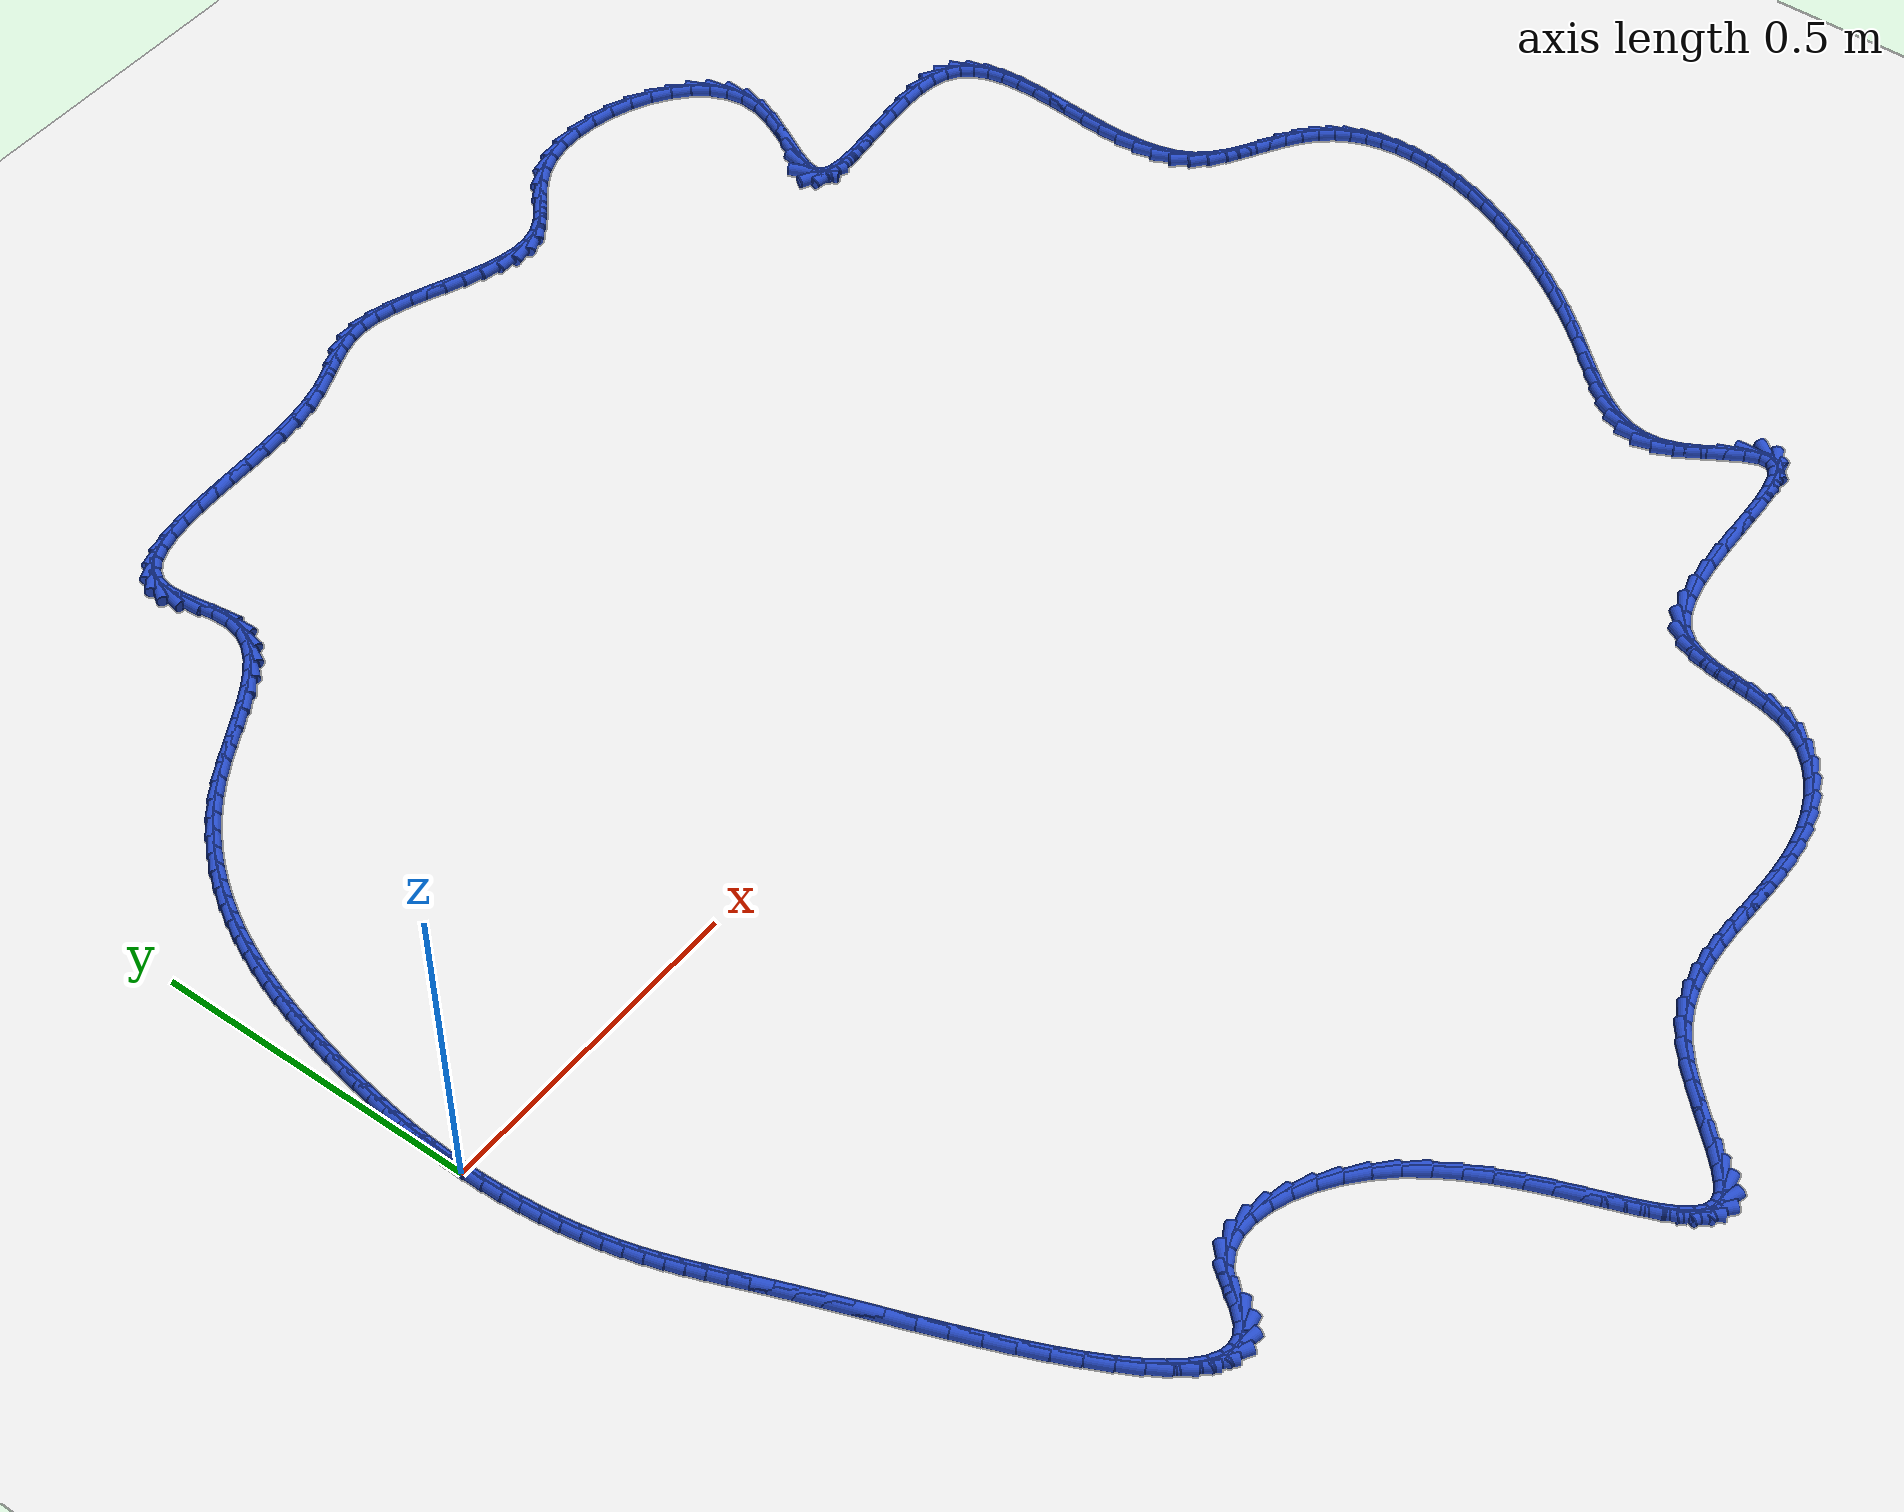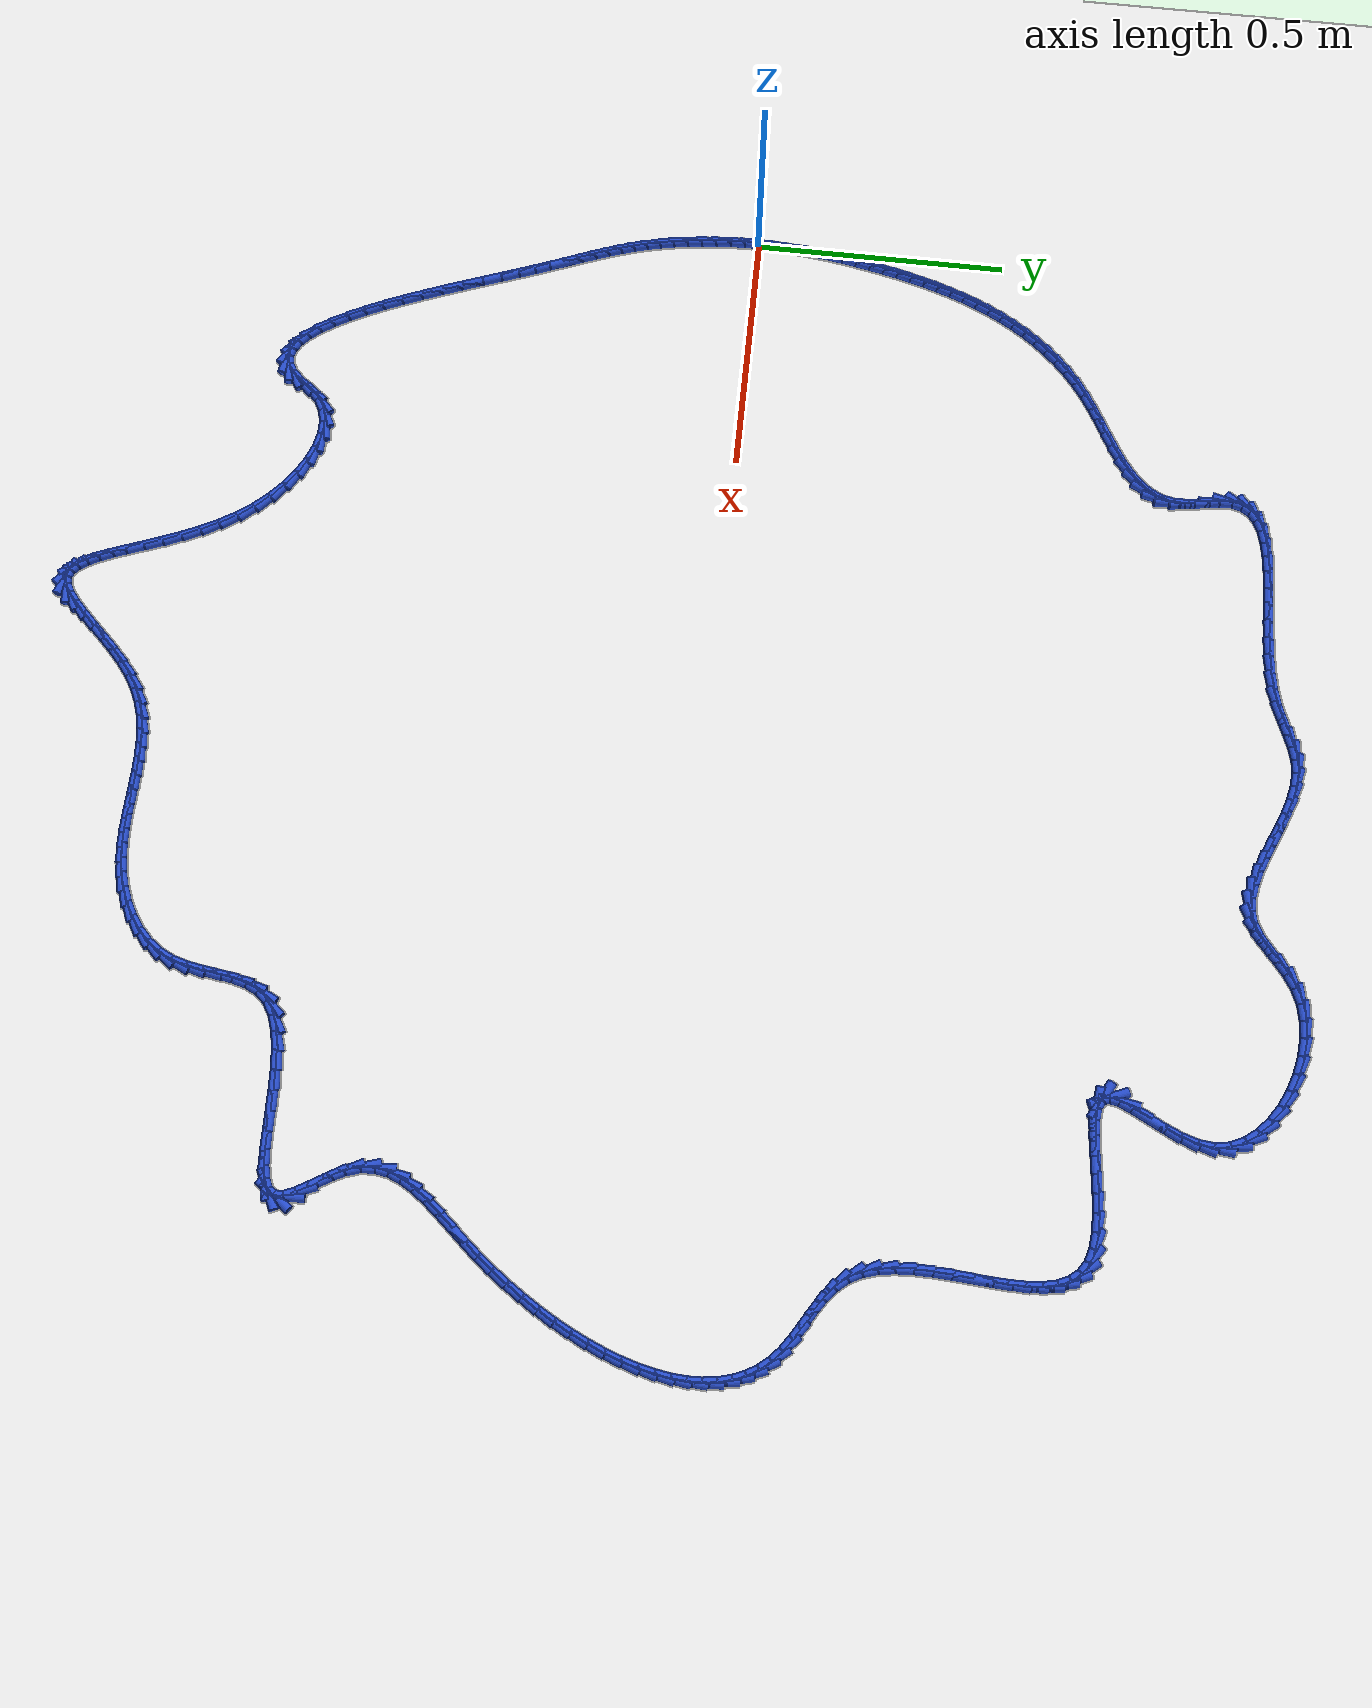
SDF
<sdf version="1.6">
 <world name="default">
  <light name="sun" type="directional">
   <pose>0 0 10 0 -0 0</pose>
   <diffuse>0.8 0.8 0.8 1</diffuse>
   <specular>0.2 0.2 0.2 1</specular>
   <attenuation>
    <range>1000</range>
    <constant>0.9</constant>
    <linear>0.01</linear>
    <quadratic>0.001</quadratic>
   </attenuation>
   <direction>-0.5 0.1 -0.9</direction>
  </light>
  <model name="ground_plane">
   <static>1</static>
   <link name="link">
    <collision name="collision">
     <geometry><plane><normal>0 0 1</normal><size>100 100</size></plane></geometry>
     <surface><friction><ode><mu>100</mu><mu2>50</mu2></ode></friction></surface>
    </collision>
    <visual name="visual">
     <cast_shadows>0</cast_shadows>
     <geometry><plane><normal>0 0 1</normal><size>100 100</size></plane></geometry>
     <material>
      <script><uri>file://media/materials/scripts/gazebo.material</uri><name>Gazebo/WhiteGlow</name></script>
     </material>
    </visual>
   </link>
  </model>
  <gravity>0 0 -9.8</gravity>
  <magnetic_field>6e-06 2.3e-05 -4.2e-05</magnetic_field>
  <atmosphere type="adiabatic"/>
  <physics name="default_physics" default="0" type="ode">
   <max_step_size>0.001</max_step_size>
   <real_time_factor>1</real_time_factor>
   <real_time_update_rate>1000</real_time_update_rate>
  </physics>
  <scene><ambient>0.4 0.4 0.4 1</ambient><background>0.7 0.7 0.7 1</background><shadows>1</shadows></scene>
  <spherical_coordinates>
   <surface_model>EARTH_WGS84</surface_model>
   <latitude_deg>0</latitude_deg>
   <longitude_deg>0</longitude_deg>
   <elevation>0</elevation>
   <heading_deg>0</heading_deg>
  </spherical_coordinates>
  <model name="line">
   <link name="link_0">
    <pose>-4.336808689942018e-18 -1.0408340855860843e-16 0.01 0 1.57 1.5462348624224949</pose>
    <collision name="collision">
     <geometry><cylinder><radius>0.01</radius><length>0.08</length></cylinder></geometry>
    </collision>
    <visual name="visual">
     <material>
      <script><name>Gazebo/Blue</name><uri>file://media/materials/scripts/gazebo.material</uri></script>
     </material>
     <geometry><cylinder><radius>0.01</radius><length>0.08</length></cylinder></geometry>
    </visual>
   </link>
   <link name="link_1">
    <pose>0.0007183228612163952 0.02924004847770259 0.01 0 1.57 1.5158970800816691</pose>
    <collision name="collision">
     <geometry><cylinder><radius>0.01</radius><length>0.08</length></cylinder></geometry>
    </collision>
    <visual name="visual">
     <material>
      <script><name>Gazebo/Blue</name><uri>file://media/materials/scripts/gazebo.material</uri></script>
     </material>
     <geometry><cylinder><radius>0.01</radius><length>0.08</length></cylinder></geometry>
    </visual>
   </link>
   <link name="link_2">
    <pose>0.0023122697255640793 0.058244912682233835 0.01 0 1.57 1.4874370785951219</pose>
    <collision name="collision">
     <geometry><cylinder><radius>0.01</radius><length>0.08</length></cylinder></geometry>
    </collision>
    <visual name="visual">
     <material>
      <script><name>Gazebo/Blue</name><uri>file://media/materials/scripts/gazebo.material</uri></script>
     </material>
     <geometry><cylinder><radius>0.01</radius><length>0.08</length></cylinder></geometry>
    </visual>
   </link>
   <link name="link_3">
    <pose>0.004719690675577835 0.08705805839520586 0.01 0 1.57 1.4610435413965277</pose>
    <collision name="collision">
     <geometry><cylinder><radius>0.01</radius><length>0.08</length></cylinder></geometry>
    </collision>
    <visual name="visual">
     <material>
      <script><name>Gazebo/Blue</name><uri>file://media/materials/scripts/gazebo.material</uri></script>
     </material>
     <geometry><cylinder><radius>0.01</radius><length>0.08</length></cylinder></geometry>
    </visual>
   </link>
   <link name="link_4">
    <pose>0.007878435793792452 0.11572295139823095 0.01 0 1.57 1.4368722158770506</pose>
    <collision name="collision">
     <geometry><cylinder><radius>0.01</radius><length>0.08</length></cylinder></geometry>
    </collision>
    <visual name="visual">
     <material>
      <script><name>Gazebo/Blue</name><uri>file://media/materials/scripts/gazebo.material</uri></script>
     </material>
     <geometry><cylinder><radius>0.01</radius><length>0.08</length></cylinder></geometry>
    </visual>
   </link>
   <link name="link_5">
    <pose>0.011726355162742714 0.1442830574729213 0.01 0 1.57 1.4150458155403258</pose>
    <collision name="collision">
     <geometry><cylinder><radius>0.01</radius><length>0.08</length></cylinder></geometry>
    </collision>
    <visual name="visual">
     <material>
      <script><name>Gazebo/Blue</name><uri>file://media/materials/scripts/gazebo.material</uri></script>
     </material>
     <geometry><cylinder><radius>0.01</radius><length>0.08</length></cylinder></geometry>
    </visual>
   </link>
   <link name="link_6">
    <pose>0.01620129886496342 0.1727818424008893 0.01 0 1.57 1.395655228277873</pose>
    <collision name="collision">
     <geometry><cylinder><radius>0.01</radius><length>0.08</length></cylinder></geometry>
    </collision>
    <visual name="visual">
     <material>
      <script><name>Gazebo/Blue</name><uri>file://media/materials/scripts/gazebo.material</uri></script>
     </material>
     <geometry><cylinder><radius>0.01</radius><length>0.08</length></cylinder></geometry>
    </visual>
   </link>
   <link name="link_7">
    <pose>0.021241116982989344 0.20126277196374703 0.01 0 1.57 1.378761685349251</pose>
    <collision name="collision">
     <geometry><cylinder><radius>0.01</radius><length>0.08</length></cylinder></geometry>
    </collision>
    <visual name="visual">
     <material>
      <script><name>Gazebo/Blue</name><uri>file://media/materials/scripts/gazebo.material</uri></script>
     </material>
     <geometry><cylinder><radius>0.01</radius><length>0.08</length></cylinder></geometry>
    </visual>
   </link>
   <link name="link_8">
    <pose>0.026783659599355282 0.22976931194310682 0.01 0 1.57 1.3635401479682643</pose>
    <collision name="collision">
     <geometry><cylinder><radius>0.01</radius><length>0.08</length></cylinder></geometry>
    </collision>
    <visual name="visual">
     <material>
      <script><name>Gazebo/Blue</name><uri>file://media/materials/scripts/gazebo.material</uri></script>
     </material>
     <geometry><cylinder><radius>0.01</radius><length>0.08</length></cylinder></geometry>
    </visual>
   </link>
   <link name="link_9">
    <pose>0.0327886819730688 0.2583271721288659 0.01 0 1.57 1.3462293695382168</pose>
    <collision name="collision">
     <geometry><cylinder><radius>0.01</radius><length>0.08</length></cylinder></geometry>
    </collision>
    <visual name="visual">
     <material>
      <script><name>Gazebo/Blue</name><uri>file://media/materials/scripts/gazebo.material</uri></script>
     </material>
     <geometry><cylinder><radius>0.01</radius><length>0.08</length></cylinder></geometry>
    </visual>
   </link>
   <link name="link_10">
    <pose>0.03931172046097369 0.28688442365862715 0.01 0 1.57 1.3257552817674427</pose>
    <collision name="collision">
     <geometry><cylinder><radius>0.01</radius><length>0.08</length></cylinder></geometry>
    </collision>
    <visual name="visual">
     <material>
      <script><name>Gazebo/Blue</name><uri>file://media/materials/scripts/gazebo.material</uri></script>
     </material>
     <geometry><cylinder><radius>0.01</radius><length>0.08</length></cylinder></geometry>
    </visual>
   </link>
   <link name="link_11">
    <pose>0.04643448327744529 0.315367923173681 0.01 0 1.57 1.3020485892004672</pose>
    <collision name="collision">
     <geometry><cylinder><radius>0.01</radius><length>0.08</length></cylinder></geometry>
    </collision>
    <visual name="visual">
     <material>
      <script><name>Gazebo/Blue</name><uri>file://media/materials/scripts/gazebo.material</uri></script>
     </material>
     <geometry><cylinder><radius>0.01</radius><length>0.08</length></cylinder></geometry>
    </visual>
   </link>
   <link name="link_12">
    <pose>0.054238679262937656 0.3437045268078285 0.01 0 1.57 1.2750260112713936</pose>
    <collision name="collision">
     <geometry><cylinder><radius>0.01</radius><length>0.08</length></cylinder></geometry>
    </collision>
    <visual name="visual">
     <material>
      <script><name>Gazebo/Blue</name><uri>file://media/materials/scripts/gazebo.material</uri></script>
     </material>
     <geometry><cylinder><radius>0.01</radius><length>0.08</length></cylinder></geometry>
    </visual>
   </link>
   <link name="link_13">
    <pose>0.06280601725790493 0.37182109069487074 0.01 0 1.57 1.244597310167133</pose>
    <collision name="collision">
     <geometry><cylinder><radius>0.01</radius><length>0.08</length></cylinder></geometry>
    </collision>
    <visual name="visual">
     <material>
      <script><name>Gazebo/Blue</name><uri>file://media/materials/scripts/gazebo.material</uri></script>
     </material>
     <geometry><cylinder><radius>0.01</radius><length>0.08</length></cylinder></geometry>
    </visual>
   </link>
   <link name="link_14">
    <pose>0.07221820610280122 0.3996444709686088 0.01 0 1.57 1.210673974683876</pose>
    <collision name="collision">
     <geometry><cylinder><radius>0.01</radius><length>0.08</length></cylinder></geometry>
    </collision>
    <visual name="visual">
     <material>
      <script><name>Gazebo/Blue</name><uri>file://media/materials/scripts/gazebo.material</uri></script>
     </material>
     <geometry><cylinder><radius>0.01</radius><length>0.08</length></cylinder></geometry>
    </visual>
   </link>
   <link name="link_15">
    <pose>0.0825569546380806 0.4271015237628437 0.01 0 1.57 1.1731798866829903</pose>
    <collision name="collision">
     <geometry><cylinder><radius>0.01</radius><length>0.08</length></cylinder></geometry>
    </collision>
    <visual name="visual">
     <material>
      <script><name>Gazebo/Blue</name><uri>file://media/materials/scripts/gazebo.material</uri></script>
     </material>
     <geometry><cylinder><radius>0.01</radius><length>0.08</length></cylinder></geometry>
    </visual>
   </link>
   <link name="link_16">
    <pose>0.09390397170419716 0.4541191052113763 0.01 0 1.57 1.1320641711577684</pose>
    <collision name="collision">
     <geometry><cylinder><radius>0.01</radius><length>0.08</length></cylinder></geometry>
    </collision>
    <visual name="visual">
     <material>
      <script><name>Gazebo/Blue</name><uri>file://media/materials/scripts/gazebo.material</uri></script>
     </material>
     <geometry><cylinder><radius>0.01</radius><length>0.08</length></cylinder></geometry>
    </visual>
   </link>
   <link name="link_17">
    <pose>0.1063409661416051 0.4806240714480081 0.01 0 1.57 1.0873161502114705</pose>
    <collision name="collision">
     <geometry><cylinder><radius>0.01</radius><length>0.08</length></cylinder></geometry>
    </collision>
    <visual name="visual">
     <material>
      <script><name>Gazebo/Blue</name><uri>file://media/materials/scripts/gazebo.material</uri></script>
     </material>
     <geometry><cylinder><radius>0.01</radius><length>0.08</length></cylinder></geometry>
    </visual>
   </link>
   <link name="link_18">
    <pose>0.11994964679075837 0.5065432786065397 0.01 0 1.57 1.0389818778242934</pose>
    <collision name="collision">
     <geometry><cylinder><radius>0.01</radius><length>0.08</length></cylinder></geometry>
    </collision>
    <visual name="visual">
     <material>
      <script><name>Gazebo/Blue</name><uri>file://media/materials/scripts/gazebo.material</uri></script>
     </material>
     <geometry><cylinder><radius>0.01</radius><length>0.08</length></cylinder></geometry>
    </visual>
   </link>
   <link name="link_19">
    <pose>0.1348117224921112 0.5318035828207723 0.01 0 1.57 0.9871811251425942</pose>
    <collision name="collision">
     <geometry><cylinder><radius>0.01</radius><length>0.08</length></cylinder></geometry>
    </collision>
    <visual name="visual">
     <material>
      <script><name>Gazebo/Blue</name><uri>file://media/materials/scripts/gazebo.material</uri></script>
     </material>
     <geometry><cylinder><radius>0.01</radius><length>0.08</length></cylinder></geometry>
    </visual>
   </link>
   <link name="link_20">
    <pose>0.15100890208611756 0.556331840224507 0.01 0 1.57 0.9321229770418913</pose>
    <collision name="collision">
     <geometry><cylinder><radius>0.01</radius><length>0.08</length></cylinder></geometry>
    </collision>
    <visual name="visual">
     <material>
      <script><name>Gazebo/Blue</name><uri>file://media/materials/scripts/gazebo.material</uri></script>
     </material>
     <geometry><cylinder><radius>0.01</radius><length>0.08</length></cylinder></geometry>
    </visual>
   </link>
   <link name="link_21">
    <pose>0.16862289441323175 0.5800549069515448 0.01 0 1.57 0.8741175440049855</pose>
    <collision name="collision">
     <geometry><cylinder><radius>0.01</radius><length>0.08</length></cylinder></geometry>
    </collision>
    <visual name="visual">
     <material>
      <script><name>Gazebo/Blue</name><uri>file://media/materials/scripts/gazebo.material</uri></script>
     </material>
     <geometry><cylinder><radius>0.01</radius><length>0.08</length></cylinder></geometry>
    </visual>
   </link>
   <link name="link_22">
    <pose>0.18773540831390773 0.6028996391356868 0.01 0 1.57 0.8135809383694007</pose>
    <collision name="collision">
     <geometry><cylinder><radius>0.01</radius><length>0.08</length></cylinder></geometry>
    </collision>
    <visual name="visual">
     <material>
      <script><name>Gazebo/Blue</name><uri>file://media/materials/scripts/gazebo.material</uri></script>
     </material>
     <geometry><cylinder><radius>0.01</radius><length>0.08</length></cylinder></geometry>
    </visual>
   </link>
   <link name="link_23">
    <pose>0.20842815262859957 0.624792892910734 0.01 0 1.57 0.7510309021639047</pose>
    <collision name="collision">
     <geometry><cylinder><radius>0.01</radius><length>0.08</length></cylinder></geometry>
    </collision>
    <visual name="visual">
     <material>
      <script><name>Gazebo/Blue</name><uri>file://media/materials/scripts/gazebo.material</uri></script>
     </material>
     <geometry><cylinder><radius>0.01</radius><length>0.08</length></cylinder></geometry>
    </visual>
   </link>
   <link name="link_24">
    <pose>0.2307828361977615 0.6456615244104875 0.01 0 1.57 0.6870715143448622</pose>
    <collision name="collision">
     <geometry><cylinder><radius>0.01</radius><length>0.08</length></cylinder></geometry>
    </collision>
    <visual name="visual">
     <material>
      <script><name>Gazebo/Blue</name><uri>file://media/materials/scripts/gazebo.material</uri></script>
     </material>
     <geometry><cylinder><radius>0.01</radius><length>0.08</length></cylinder></geometry>
    </visual>
   </link>
   <link name="link_25">
    <pose>0.25488116786184756 0.6654323897687481 0.01 0 1.57 0.6223672143764937</pose>
    <collision name="collision">
     <geometry><cylinder><radius>0.01</radius><length>0.08</length></cylinder></geometry>
    </collision>
    <visual name="visual">
     <material>
      <script><name>Gazebo/Blue</name><uri>file://media/materials/scripts/gazebo.material</uri></script>
     </material>
     <geometry><cylinder><radius>0.01</radius><length>0.08</length></cylinder></geometry>
    </visual>
   </link>
   <link name="link_26">
    <pose>0.28080485646131176 0.6840323451193171 0.01 0 1.57 0.5607926366893917</pose>
    <collision name="collision">
     <geometry><cylinder><radius>0.01</radius><length>0.08</length></cylinder></geometry>
    </collision>
    <visual name="visual">
     <material>
      <script><name>Gazebo/Blue</name><uri>file://media/materials/scripts/gazebo.material</uri></script>
     </material>
     <geometry><cylinder><radius>0.01</radius><length>0.08</length></cylinder></geometry>
    </visual>
   </link>
   <link name="link_27">
    <pose>0.30852955385874453 0.7014449599614958 0.01 0 1.57 0.5205593701171067</pose>
    <collision name="collision">
     <geometry><cylinder><radius>0.01</radius><length>0.08</length></cylinder></geometry>
    </collision>
    <visual name="visual">
     <material>
      <script><name>Gazebo/Blue</name><uri>file://media/materials/scripts/gazebo.material</uri></script>
     </material>
     <geometry><cylinder><radius>0.01</radius><length>0.08</length></cylinder></geometry>
    </visual>
   </link>
   <link name="link_28">
    <pose>0.33739517585041395 0.7179937600390222 0.01 0 1.57 0.5061011511809811</pose>
    <collision name="collision">
     <geometry><cylinder><radius>0.01</radius><length>0.08</length></cylinder></geometry>
    </collision>
    <visual name="visual">
     <material>
      <script><name>Gazebo/Blue</name><uri>file://media/materials/scripts/gazebo.material</uri></script>
     </material>
     <geometry><cylinder><radius>0.01</radius><length>0.08</length></cylinder></geometry>
    </visual>
   </link>
   <link name="link_29">
    <pose>0.36650582641331186 0.7341283701243384 0.01 0 1.57 0.5166988833297147</pose>
    <collision name="collision">
     <geometry><cylinder><radius>0.01</radius><length>0.08</length></cylinder></geometry>
    </collision>
    <visual name="visual">
     <material>
      <script><name>Gazebo/Blue</name><uri>file://media/materials/scripts/gazebo.material</uri></script>
     </material>
     <geometry><cylinder><radius>0.01</radius><length>0.08</length></cylinder></geometry>
    </visual>
   </link>
   <link name="link_30">
    <pose>0.3949652219921632 0.7502986222205614 0.01 0 1.57 0.5542001710778023</pose>
    <collision name="collision">
     <geometry><cylinder><radius>0.01</radius><length>0.08</length></cylinder></geometry>
    </collision>
    <visual name="visual">
     <material>
      <script><name>Gazebo/Blue</name><uri>file://media/materials/scripts/gazebo.material</uri></script>
     </material>
     <geometry><cylinder><radius>0.01</radius><length>0.08</length></cylinder></geometry>
    </visual>
   </link>
   <link name="link_31">
    <pose>0.4218770790316925 0.7669543483308078 0.01 0 1.57 0.6233241429852437</pose>
    <collision name="collision">
     <geometry><cylinder><radius>0.01</radius><length>0.08</length></cylinder></geometry>
    </collision>
    <visual name="visual">
     <material>
      <script><name>Gazebo/Blue</name><uri>file://media/materials/scripts/gazebo.material</uri></script>
     </material>
     <geometry><cylinder><radius>0.01</radius><length>0.08</length></cylinder></geometry>
    </visual>
   </link>
   <link name="link_32">
    <pose>0.4463451139766249 0.7845453804581949 0.01 0 1.57 0.7317952171511489</pose>
    <collision name="collision">
     <geometry><cylinder><radius>0.01</radius><length>0.08</length></cylinder></geometry>
    </collision>
    <visual name="visual">
     <material>
      <script><name>Gazebo/Blue</name><uri>file://media/materials/scripts/gazebo.material</uri></script>
     </material>
     <geometry><cylinder><radius>0.01</radius><length>0.08</length></cylinder></geometry>
    </visual>
   </link>
   <link name="link_33">
    <pose>0.4674730432716852 0.8035215506058394 0.01 0 1.57 0.8889868237704391</pose>
    <collision name="collision">
     <geometry><cylinder><radius>0.01</radius><length>0.08</length></cylinder></geometry>
    </collision>
    <visual name="visual">
     <material>
      <script><name>Gazebo/Blue</name><uri>file://media/materials/scripts/gazebo.material</uri></script>
     </material>
     <geometry><cylinder><radius>0.01</radius><length>0.08</length></cylinder></geometry>
    </visual>
   </link>
   <link name="link_34">
    <pose>0.48436458336159793 0.8243326907768579 0.01 0 1.57 1.0998703822961402</pose>
    <collision name="collision">
     <geometry><cylinder><radius>0.01</radius><length>0.08</length></cylinder></geometry>
    </collision>
    <visual name="visual">
     <material>
      <script><name>Gazebo/Blue</name><uri>file://media/materials/scripts/gazebo.material</uri></script>
     </material>
     <geometry><cylinder><radius>0.01</radius><length>0.08</length></cylinder></geometry>
    </visual>
   </link>
   <link name="link_35">
    <pose>0.4961234506910881 0.8474286329743677 0.01 0 1.57 1.3525043392201155</pose>
    <collision name="collision">
     <geometry><cylinder><radius>0.01</radius><length>0.08</length></cylinder></geometry>
    </collision>
    <visual name="visual">
     <material>
      <script><name>Gazebo/Blue</name><uri>file://media/materials/scripts/gazebo.material</uri></script>
     </material>
     <geometry><cylinder><radius>0.01</radius><length>0.08</length></cylinder></geometry>
    </visual>
   </link>
   <link name="link_36">
    <pose>0.5018533617048805 0.8732592092014854 0.01 0 1.57 -1.5458113672183387</pose>
    <collision name="collision">
     <geometry><cylinder><radius>0.01</radius><length>0.08</length></cylinder></geometry>
    </collision>
    <visual name="visual">
     <material>
      <script><name>Gazebo/Blue</name><uri>file://media/materials/scripts/gazebo.material</uri></script>
     </material>
     <geometry><cylinder><radius>0.01</radius><length>0.08</length></cylinder></geometry>
    </visual>
   </link>
   <link name="link_37">
    <pose>0.5011351351879454 0.9019995823038233 0.01 0 1.57 -1.4193034929931134</pose>
    <collision name="collision">
     <geometry><cylinder><radius>0.01</radius><length>0.08</length></cylinder></geometry>
    </collision>
    <visual name="visual">
     <material>
      <script><name>Gazebo/Blue</name><uri>file://media/materials/scripts/gazebo.material</uri></script>
     </material>
     <geometry><cylinder><radius>0.01</radius><length>0.08</length></cylinder></geometry>
    </visual>
   </link>
   <link name="link_38">
    <pose>0.4965393665960186 0.9321036922990686 0.01 0 1.57 -1.409940151759371</pose>
    <collision name="collision">
     <geometry><cylinder><radius>0.01</radius><length>0.08</length></cylinder></geometry>
    </collision>
    <visual name="visual">
     <material>
      <script><name>Gazebo/Blue</name><uri>file://media/materials/scripts/gazebo.material</uri></script>
     </material>
     <geometry><cylinder><radius>0.01</radius><length>0.08</length></cylinder></geometry>
    </visual>
   </link>
   <link name="link_39">
    <pose>0.4917922642409274 0.9613601896374306 0.01 0 1.57 -1.5261320822971656</pose>
    <collision name="collision">
     <geometry><cylinder><radius>0.01</radius><length>0.08</length></cylinder></geometry>
    </collision>
    <visual name="visual">
     <material>
      <script><name>Gazebo/Blue</name><uri>file://media/materials/scripts/gazebo.material</uri></script>
     </material>
     <geometry><cylinder><radius>0.01</radius><length>0.08</length></cylinder></geometry>
    </visual>
   </link>
   <link name="link_40">
    <pose>0.4906214256611757 0.9875569813389942 0.01 0 1.57 1.3373394361693471</pose>
    <collision name="collision">
     <geometry><cylinder><radius>0.01</radius><length>0.08</length></cylinder></geometry>
    </collision>
    <visual name="visual">
     <material>
      <script><name>Gazebo/Blue</name><uri>file://media/materials/scripts/gazebo.material</uri></script>
     </material>
     <geometry><cylinder><radius>0.01</radius><length>0.08</length></cylinder></geometry>
    </visual>
   </link>
   <link name="link_41">
    <pose>0.4957473855238994 1.0091134001234727 0.01 0 1.57 0.9887500694723694</pose>
    <collision name="collision">
     <geometry><cylinder><radius>0.01</radius><length>0.08</length></cylinder></geometry>
    </collision>
    <visual name="visual">
     <material>
      <script><name>Gazebo/Blue</name><uri>file://media/materials/scripts/gazebo.material</uri></script>
     </material>
     <geometry><cylinder><radius>0.01</radius><length>0.08</length></cylinder></geometry>
    </visual>
   </link>
   <link name="link_42">
    <pose>0.5070228781272357 1.0262468817941888 0.01 0 1.57 0.6685071533585554</pose>
    <collision name="collision">
     <geometry><cylinder><radius>0.01</radius><length>0.08</length></cylinder></geometry>
    </collision>
    <visual name="visual">
     <material>
      <script><name>Gazebo/Blue</name><uri>file://media/materials/scripts/gazebo.material</uri></script>
     </material>
     <geometry><cylinder><radius>0.01</radius><length>0.08</length></cylinder></geometry>
    </visual>
   </link>
   <link name="link_43">
    <pose>0.5237935432515232 1.0394928090471414 0.01 0 1.57 0.42932225369989446</pose>
    <collision name="collision">
     <geometry><cylinder><radius>0.01</radius><length>0.08</length></cylinder></geometry>
    </collision>
    <visual name="visual">
     <material>
      <script><name>Gazebo/Blue</name><uri>file://media/materials/scripts/gazebo.material</uri></script>
     </material>
     <geometry><cylinder><radius>0.01</radius><length>0.08</length></cylinder></geometry>
    </visual>
   </link>
   <link name="link_44">
    <pose>0.5454050206771001 1.049386564578328 0.01 0 1.57 0.26773673978531026</pose>
    <collision name="collision">
     <geometry><cylinder><radius>0.01</radius><length>0.08</length></cylinder></geometry>
    </collision>
    <visual name="visual">
     <material>
      <script><name>Gazebo/Blue</name><uri>file://media/materials/scripts/gazebo.material</uri></script>
     </material>
     <geometry><cylinder><radius>0.01</radius><length>0.08</length></cylinder></geometry>
    </visual>
   </link>
   <link name="link_45">
    <pose>0.5712029501843049 1.0564635310837467 0.01 0 1.57 0.16206939965983158</pose>
    <collision name="collision">
     <geometry><cylinder><radius>0.01</radius><length>0.08</length></cylinder></geometry>
    </collision>
    <visual name="visual">
     <material>
      <script><name>Gazebo/Blue</name><uri>file://media/materials/scripts/gazebo.material</uri></script>
     </material>
     <geometry><cylinder><radius>0.01</radius><length>0.08</length></cylinder></geometry>
    </visual>
   </link>
   <link name="link_46">
    <pose>0.6005329715534757 1.0612590912593953 0.01 0 1.57 0.09440187548298841</pose>
    <collision name="collision">
     <geometry><cylinder><radius>0.01</radius><length>0.08</length></cylinder></geometry>
    </collision>
    <visual name="visual">
     <material>
      <script><name>Gazebo/Blue</name><uri>file://media/materials/scripts/gazebo.material</uri></script>
     </material>
     <geometry><cylinder><radius>0.01</radius><length>0.08</length></cylinder></geometry>
    </visual>
   </link>
   <link name="link_47">
    <pose>0.6327407245649517 1.0643086278012726 0.01 0 1.57 0.05335725142116658</pose>
    <collision name="collision">
     <geometry><cylinder><radius>0.01</radius><length>0.08</length></cylinder></geometry>
    </collision>
    <visual name="visual">
     <material>
      <script><name>Gazebo/Blue</name><uri>file://media/materials/scripts/gazebo.material</uri></script>
     </material>
     <geometry><cylinder><radius>0.01</radius><length>0.08</length></cylinder></geometry>
    </visual>
   </link>
   <link name="link_48">
    <pose>0.6671718489990706 1.066147523405376 0.01 0 1.57 0.032311888419340885</pose>
    <collision name="collision">
     <geometry><cylinder><radius>0.01</radius><length>0.08</length></cylinder></geometry>
    </collision>
    <visual name="visual">
     <material>
      <script><name>Gazebo/Blue</name><uri>file://media/materials/scripts/gazebo.material</uri></script>
     </material>
     <geometry><cylinder><radius>0.01</radius><length>0.08</length></cylinder></geometry>
    </visual>
   </link>
   <link name="link_49">
    <pose>0.703171984636171 1.0673111607677042 0.01 0 1.57 0.02772600261981497</pose>
    <collision name="collision">
     <geometry><cylinder><radius>0.01</radius><length>0.08</length></cylinder></geometry>
    </collision>
    <visual name="visual">
     <material>
      <script><name>Gazebo/Blue</name><uri>file://media/materials/scripts/gazebo.material</uri></script>
     </material>
     <geometry><cylinder><radius>0.01</radius><length>0.08</length></cylinder></geometry>
    </visual>
   </link>
   <link name="link_50">
    <pose>0.7400867712565914 1.0683349225842542 0.01 0 1.57 0.03815943674371229</pose>
    <collision name="collision">
     <geometry><cylinder><radius>0.01</radius><length>0.08</length></cylinder></geometry>
    </collision>
    <visual name="visual">
     <material>
      <script><name>Gazebo/Blue</name><uri>file://media/materials/scripts/gazebo.material</uri></script>
     </material>
     <geometry><cylinder><radius>0.01</radius><length>0.08</length></cylinder></geometry>
    </visual>
   </link>
   <link name="link_51">
    <pose>0.77726184864067 1.0697541915510254 0.01 0 1.57 0.06380924363371977</pose>
    <collision name="collision">
     <geometry><cylinder><radius>0.01</radius><length>0.08</length></cylinder></geometry>
    </collision>
    <visual name="visual">
     <material>
      <script><name>Gazebo/Blue</name><uri>file://media/materials/scripts/gazebo.material</uri></script>
     </material>
     <geometry><cylinder><radius>0.01</radius><length>0.08</length></cylinder></geometry>
    </visual>
   </link>
   <link name="link_52">
    <pose>0.8140428565687454 1.0721043503640149 0.01 0 1.57 0.10640200698705973</pose>
    <collision name="collision">
     <geometry><cylinder><radius>0.01</radius><length>0.08</length></cylinder></geometry>
    </collision>
    <visual name="visual">
     <material>
      <script><name>Gazebo/Blue</name><uri>file://media/materials/scripts/gazebo.material</uri></script>
     </material>
     <geometry><cylinder><radius>0.01</radius><length>0.08</length></cylinder></geometry>
    </visual>
   </link>
   <link name="link_53">
    <pose>0.8497754348211561 1.075920781719221 0.01 0 1.57 0.16933315072372382</pose>
    <collision name="collision">
     <geometry><cylinder><radius>0.01</radius><length>0.08</length></cylinder></geometry>
    </collision>
    <visual name="visual">
     <material>
      <script><name>Gazebo/Blue</name><uri>file://media/materials/scripts/gazebo.material</uri></script>
     </material>
     <geometry><cylinder><radius>0.01</radius><length>0.08</length></cylinder></geometry>
    </visual>
   </link>
   <link name="link_54">
    <pose>0.8838052231782404 1.0817388683126417 0.01 0 1.57 0.25767439060480485</pose>
    <collision name="collision">
     <geometry><cylinder><radius>0.01</radius><length>0.08</length></cylinder></geometry>
    </collision>
    <visual name="visual">
     <material>
      <script><name>Gazebo/Blue</name><uri>file://media/materials/scripts/gazebo.material</uri></script>
     </material>
     <geometry><cylinder><radius>0.01</radius><length>0.08</length></cylinder></geometry>
    </visual>
   </link>
   <link name="link_55">
    <pose>0.9154824358953043 1.0900868557273622 0.01 0 1.57 0.3502906657793422</pose>
    <collision name="collision">
     <geometry><cylinder><radius>0.01</radius><length>0.08</length></cylinder></geometry>
    </collision>
    <visual name="visual">
     <material>
      <script><name>Gazebo/Blue</name><uri>file://media/materials/scripts/gazebo.material</uri></script>
     </material>
     <geometry><cylinder><radius>0.01</radius><length>0.08</length></cylinder></geometry>
    </visual>
   </link>
   <link name="link_56">
    <pose>0.9446400292977614 1.100739813567409 0.01 0 1.57 0.3923252835983964</pose>
    <collision name="collision">
     <geometry><cylinder><radius>0.01</radius><length>0.08</length></cylinder></geometry>
    </collision>
    <visual name="visual">
     <material>
      <script><name>Gazebo/Blue</name><uri>file://media/materials/scripts/gazebo.material</uri></script>
     </material>
     <geometry><cylinder><radius>0.01</radius><length>0.08</length></cylinder></geometry>
    </visual>
   </link>
   <link name="link_57">
    <pose>0.9720126763766781 1.1120659497304475 0.01 0 1.57 0.36886892560150697</pose>
    <collision name="collision">
     <geometry><cylinder><radius>0.01</radius><length>0.08</length></cylinder></geometry>
    </collision>
    <visual name="visual">
     <material>
      <script><name>Gazebo/Blue</name><uri>file://media/materials/scripts/gazebo.material</uri></script>
     </material>
     <geometry><cylinder><radius>0.01</radius><length>0.08</length></cylinder></geometry>
    </visual>
   </link>
   <link name="link_58">
    <pose>0.9984338189197063 1.1222793726691698 0.01 0 1.57 0.271243554786539</pose>
    <collision name="collision">
     <geometry><cylinder><radius>0.01</radius><length>0.08</length></cylinder></geometry>
    </collision>
    <visual name="visual">
     <material>
      <script><name>Gazebo/Blue</name><uri>file://media/materials/scripts/gazebo.material</uri></script>
     </material>
     <geometry><cylinder><radius>0.01</radius><length>0.08</length></cylinder></geometry>
    </visual>
   </link>
   <link name="link_59">
    <pose>1.024736898714498 1.1295941908362683 0.01 0 1.57 0.09850898987949476</pose>
    <collision name="collision">
     <geometry><cylinder><radius>0.01</radius><length>0.08</length></cylinder></geometry>
    </collision>
    <visual name="visual">
     <material>
      <script><name>Gazebo/Blue</name><uri>file://media/materials/scripts/gazebo.material</uri></script>
     </material>
     <geometry><cylinder><radius>0.01</radius><length>0.08</length></cylinder></geometry>
    </visual>
   </link>
   <link name="link_60">
    <pose>1.0517407963188505 1.1322629556854245 0.01 0 1.57 -0.08786865842453788</pose>
    <collision name="collision">
     <geometry><cylinder><radius>0.01</radius><length>0.08</length></cylinder></geometry>
    </collision>
    <visual name="visual">
     <material>
      <script><name>Gazebo/Blue</name><uri>file://media/materials/scripts/gazebo.material</uri></script>
     </material>
     <geometry><cylinder><radius>0.01</radius><length>0.08</length></cylinder></geometry>
    </visual>
   </link>
   <link name="link_61">
    <pose>1.0797894950598994 1.1297919915240902 0.01 0 1.57 -0.2248464791715386</pose>
    <collision name="collision">
     <geometry><cylinder><radius>0.01</radius><length>0.08</length></cylinder></geometry>
    </collision>
    <visual name="visual">
     <material>
      <script><name>Gazebo/Blue</name><uri>file://media/materials/scripts/gazebo.material</uri></script>
     </material>
     <geometry><cylinder><radius>0.01</radius><length>0.08</length></cylinder></geometry>
    </visual>
   </link>
   <link name="link_62">
    <pose>1.1086581710681542 1.1231893265571269 0.01 0 1.57 -0.3164723829564241</pose>
    <collision name="collision">
     <geometry><cylinder><radius>0.01</radius><length>0.08</length></cylinder></geometry>
    </collision>
    <visual name="visual">
     <material>
      <script><name>Gazebo/Blue</name><uri>file://media/materials/scripts/gazebo.material</uri></script>
     </material>
     <geometry><cylinder><radius>0.01</radius><length>0.08</length></cylinder></geometry>
    </visual>
   </link>
   <link name="link_63">
    <pose>1.13808846534019 1.113551524861714 0.01 0 1.57 -0.37128052685726864</pose>
    <collision name="collision">
     <geometry><cylinder><radius>0.01</radius><length>0.08</length></cylinder></geometry>
    </collision>
    <visual name="visual">
     <material>
      <script><name>Gazebo/Blue</name><uri>file://media/materials/scripts/gazebo.material</uri></script>
     </material>
     <geometry><cylinder><radius>0.01</radius><length>0.08</length></cylinder></geometry>
    </visual>
   </link>
   <link name="link_64">
    <pose>1.1678220188725787 1.1019751505150315 0.01 0 1.57 -0.39509707080164025</pose>
    <collision name="collision">
     <geometry><cylinder><radius>0.01</radius><length>0.08</length></cylinder></geometry>
    </collision>
    <visual name="visual">
     <material>
      <script><name>Gazebo/Blue</name><uri>file://media/materials/scripts/gazebo.material</uri></script>
     </material>
     <geometry><cylinder><radius>0.01</radius><length>0.08</length></cylinder></geometry>
    </visual>
   </link>
   <link name="link_65">
    <pose>1.1976004726618943 1.0895567675942597 0.01 0 1.57 -0.39031797742672675</pose>
    <collision name="collision">
     <geometry><cylinder><radius>0.01</radius><length>0.08</length></cylinder></geometry>
    </collision>
    <visual name="visual">
     <material>
      <script><name>Gazebo/Blue</name><uri>file://media/materials/scripts/gazebo.material</uri></script>
     </material>
     <geometry><cylinder><radius>0.01</radius><length>0.08</length></cylinder></geometry>
    </visual>
   </link>
   <link name="link_66">
    <pose>1.2271654677047104 1.0773929401765774 0.01 0 1.57 -0.3558373549414743</pose>
    <collision name="collision">
     <geometry><cylinder><radius>0.01</radius><length>0.08</length></cylinder></geometry>
    </collision>
    <visual name="visual">
     <material>
      <script><name>Gazebo/Blue</name><uri>file://media/materials/scripts/gazebo.material</uri></script>
     </material>
     <geometry><cylinder><radius>0.01</radius><length>0.08</length></cylinder></geometry>
    </visual>
   </link>
   <link name="link_67">
    <pose>1.2562586449975999 1.0665802323391647 0.01 0 1.57 -0.28679650120734995</pose>
    <collision name="collision">
     <geometry><cylinder><radius>0.01</radius><length>0.08</length></cylinder></geometry>
    </collision>
    <visual name="visual">
     <material>
      <script><name>Gazebo/Blue</name><uri>file://media/materials/scripts/gazebo.material</uri></script>
     </material>
     <geometry><cylinder><radius>0.01</radius><length>0.08</length></cylinder></geometry>
    </visual>
   </link>
   <link name="link_68">
    <pose>1.284621645537137 1.0582152081592013 0.01 0 1.57 -0.1743174996396374</pose>
    <collision name="collision">
     <geometry><cylinder><radius>0.01</radius><length>0.08</length></cylinder></geometry>
    </collision>
    <visual name="visual">
     <material>
      <script><name>Gazebo/Blue</name><uri>file://media/materials/scripts/gazebo.material</uri></script>
     </material>
     <geometry><cylinder><radius>0.01</radius><length>0.08</length></cylinder></geometry>
    </visual>
   </link>
   <link name="link_69">
    <pose>1.311996110319894 1.0533944317138668 0.01 0 1.57 -0.006887811893826387</pose>
    <collision name="collision">
     <geometry><cylinder><radius>0.01</radius><length>0.08</length></cylinder></geometry>
    </collision>
    <visual name="visual">
     <material>
      <script><name>Gazebo/Blue</name><uri>file://media/materials/scripts/gazebo.material</uri></script>
     </material>
     <geometry><cylinder><radius>0.01</radius><length>0.08</length></cylinder></geometry>
    </visual>
   </link>
   <link name="link_70">
    <pose>1.3381236803424452 1.0532144670803418 0.01 0 1.57 0.221986582166014</pose>
    <collision name="collision">
     <geometry><cylinder><radius>0.01</radius><length>0.08</length></cylinder></geometry>
    </collision>
    <visual name="visual">
     <material>
      <script><name>Gazebo/Blue</name><uri>file://media/materials/scripts/gazebo.material</uri></script>
     </material>
     <geometry><cylinder><radius>0.01</radius><length>0.08</length></cylinder></geometry>
    </visual>
   </link>
   <link name="link_71">
    <pose>1.3627459966013633 1.0587718783358047 0.01 0 1.57 0.4767244293590427</pose>
    <collision name="collision">
     <geometry><cylinder><radius>0.01</radius><length>0.08</length></cylinder></geometry>
    </collision>
    <visual name="visual">
     <material>
      <script><name>Gazebo/Blue</name><uri>file://media/materials/scripts/gazebo.material</uri></script>
     </material>
     <geometry><cylinder><radius>0.01</radius><length>0.08</length></cylinder></geometry>
    </visual>
   </link>
   <link name="link_72">
    <pose>1.3857884883967169 1.070672278066453 0.01 0 1.57 0.6399977336407191</pose>
    <collision name="collision">
     <geometry><cylinder><radius>0.01</radius><length>0.08</length></cylinder></geometry>
    </collision>
    <visual name="visual">
     <material>
      <script><name>Gazebo/Blue</name><uri>file://media/materials/scripts/gazebo.material</uri></script>
     </material>
     <geometry><cylinder><radius>0.01</radius><length>0.08</length></cylinder></geometry>
    </visual>
   </link>
   <link name="link_73">
    <pose>1.4080328051476627 1.0872340683228545 0.01 0 1.57 0.6985402042022182</pose>
    <collision name="collision">
     <geometry><cylinder><radius>0.01</radius><length>0.08</length></cylinder></geometry>
    </collision>
    <visual name="visual">
     <material>
      <script><name>Gazebo/Blue</name><uri>file://media/materials/scripts/gazebo.material</uri></script>
     </material>
     <geometry><cylinder><radius>0.01</radius><length>0.08</length></cylinder></geometry>
    </visual>
   </link>
   <link name="link_74">
    <pose>1.4305097423634245 1.1061101101931508 0.01 0 1.57 0.6708964162193518</pose>
    <collision name="collision">
     <geometry><cylinder><radius>0.01</radius><length>0.08</length></cylinder></geometry>
    </collision>
    <visual name="visual">
     <material>
      <script><name>Gazebo/Blue</name><uri>file://media/materials/scripts/gazebo.material</uri></script>
     </material>
     <geometry><cylinder><radius>0.01</radius><length>0.08</length></cylinder></geometry>
    </visual>
   </link>
   <link name="link_75">
    <pose>1.4542501236224572 1.1249531897844829 0.01 0 1.57 0.563864327290396</pose>
    <collision name="collision">
     <geometry><cylinder><radius>0.01</radius><length>0.08</length></cylinder></geometry>
    </collision>
    <visual name="visual">
     <material>
      <script><name>Gazebo/Blue</name><uri>file://media/materials/scripts/gazebo.material</uri></script>
     </material>
     <geometry><cylinder><radius>0.01</radius><length>0.08</length></cylinder></geometry>
    </visual>
   </link>
   <link name="link_76">
    <pose>1.4802847725032149 1.1414160932039907 0.01 0 1.57 0.38503338932570086</pose>
    <collision name="collision">
     <geometry><cylinder><radius>0.01</radius><length>0.08</length></cylinder></geometry>
    </collision>
    <visual name="visual">
     <material>
      <script><name>Gazebo/Blue</name><uri>file://media/materials/scripts/gazebo.material</uri></script>
     </material>
     <geometry><cylinder><radius>0.01</radius><length>0.08</length></cylinder></geometry>
    </visual>
   </link>
   <link name="link_77">
    <pose>1.5095480952430602 1.1532753736139638 0.01 0 1.57 0.2002234331399412</pose>
    <collision name="collision">
     <geometry><cylinder><radius>0.01</radius><length>0.08</length></cylinder></geometry>
    </collision>
    <visual name="visual">
     <material>
      <script><name>Gazebo/Blue</name><uri>file://media/materials/scripts/gazebo.material</uri></script>
     </material>
     <geometry><cylinder><radius>0.01</radius><length>0.08</length></cylinder></geometry>
    </visual>
   </link>
   <link name="link_78">
    <pose>1.541796353471404 1.1598199209307942 0.01 0 1.57 0.04472005962416173</pose>
    <collision name="collision">
     <geometry><cylinder><radius>0.01</radius><length>0.08</length></cylinder></geometry>
    </collision>
    <visual name="visual">
     <material>
      <script><name>Gazebo/Blue</name><uri>file://media/materials/scripts/gazebo.material</uri></script>
     </material>
     <geometry><cylinder><radius>0.01</radius><length>0.08</length></cylinder></geometry>
    </visual>
   </link>
   <link name="link_79">
    <pose>1.5759975953621537 1.1613504229187666 0.01 0 1.57 -0.08988787772329254</pose>
    <collision name="collision">
     <geometry><cylinder><radius>0.01</radius><length>0.08</length></cylinder></geometry>
    </collision>
    <visual name="visual">
     <material>
      <script><name>Gazebo/Blue</name><uri>file://media/materials/scripts/gazebo.material</uri></script>
     </material>
     <geometry><cylinder><radius>0.01</radius><length>0.08</length></cylinder></geometry>
    </visual>
   </link>
   <link name="link_80">
    <pose>1.6111054090250545 1.1581861291437923 0.01 0 1.57 -0.21236993503669752</pose>
    <collision name="collision">
     <geometry><cylinder><radius>0.01</radius><length>0.08</length></cylinder></geometry>
    </collision>
    <visual name="visual">
     <material>
      <script><name>Gazebo/Blue</name><uri>file://media/materials/scripts/gazebo.material</uri></script>
     </material>
     <geometry><cylinder><radius>0.01</radius><length>0.08</length></cylinder></geometry>
    </visual>
   </link>
   <link name="link_81">
    <pose>1.6460733825698528 1.150646289171782 0.01 0 1.57 -0.3306636942626501</pose>
    <collision name="collision">
     <geometry><cylinder><radius>0.01</radius><length>0.08</length></cylinder></geometry>
    </collision>
    <visual name="visual">
     <material>
      <script><name>Gazebo/Blue</name><uri>file://media/materials/scripts/gazebo.material</uri></script>
     </material>
     <geometry><cylinder><radius>0.01</radius><length>0.08</length></cylinder></geometry>
    </visual>
   </link>
   <link name="link_82">
    <pose>1.679855104106293 1.1390501525686467 0.01 0 1.57 -0.45239377221883426</pose>
    <collision name="collision">
     <geometry><cylinder><radius>0.01</radius><length>0.08</length></cylinder></geometry>
    </collision>
    <visual name="visual">
     <material>
      <script><name>Gazebo/Blue</name><uri>file://media/materials/scripts/gazebo.material</uri></script>
     </material>
     <geometry><cylinder><radius>0.01</radius><length>0.08</length></cylinder></geometry>
    </visual>
   </link>
   <link name="link_83">
    <pose>1.7114041617441207 1.123716968900298 0.01 0 1.57 -0.5856559827393523</pose>
    <collision name="collision">
     <geometry><cylinder><radius>0.01</radius><length>0.08</length></cylinder></geometry>
    </collision>
    <visual name="visual">
     <material>
      <script><name>Gazebo/Blue</name><uri>file://media/materials/scripts/gazebo.material</uri></script>
     </material>
     <geometry><cylinder><radius>0.01</radius><length>0.08</length></cylinder></geometry>
    </visual>
   </link>
   <link name="link_84">
    <pose>1.739674143593081 1.1049659877326468 0.01 0 1.57 -0.7396824722148133</pose>
    <collision name="collision">
     <geometry><cylinder><radius>0.01</radius><length>0.08</length></cylinder></geometry>
    </collision>
    <visual name="visual">
     <material>
      <script><name>Gazebo/Blue</name><uri>file://media/materials/scripts/gazebo.material</uri></script>
     </material>
     <geometry><cylinder><radius>0.01</radius><length>0.08</length></cylinder></geometry>
    </visual>
   </link>
   <link name="link_85">
    <pose>1.7636186377629195 1.0831164586316042 0.01 0 1.57 -0.9246764864221432</pose>
    <collision name="collision">
     <geometry><cylinder><radius>0.01</radius><length>0.08</length></cylinder></geometry>
    </collision>
    <visual name="visual">
     <material>
      <script><name>Gazebo/Blue</name><uri>file://media/materials/scripts/gazebo.material</uri></script>
     </material>
     <geometry><cylinder><radius>0.01</radius><length>0.08</length></cylinder></geometry>
    </visual>
   </link>
   <link name="link_86">
    <pose>1.7821912323633817 1.0584876311630815 0.01 0 1.57 -1.1490392380997279</pose>
    <collision name="collision">
     <geometry><cylinder><radius>0.01</radius><length>0.08</length></cylinder></geometry>
    </collision>
    <visual name="visual">
     <material>
      <script><name>Gazebo/Blue</name><uri>file://media/materials/scripts/gazebo.material</uri></script>
     </material>
     <geometry><cylinder><radius>0.01</radius><length>0.08</length></cylinder></geometry>
    </visual>
   </link>
   <link name="link_87">
    <pose>1.794345515504212 1.0313987548929893 0.01 0 1.57 -1.411713722811393</pose>
    <collision name="collision">
     <geometry><cylinder><radius>0.01</radius><length>0.08</length></cylinder></geometry>
    </collision>
    <visual name="visual">
     <material>
      <script><name>Gazebo/Blue</name><uri>file://media/materials/scripts/gazebo.material</uri></script>
     </material>
     <geometry><cylinder><radius>0.01</radius><length>0.08</length></cylinder></geometry>
    </visual>
   </link>
   <link name="link_88">
    <pose>1.7990350752951567 1.002169079387239 0.01 0 1.57 1.4566985335978342</pose>
    <collision name="collision">
     <geometry><cylinder><radius>0.01</radius><length>0.08</length></cylinder></geometry>
    </collision>
    <visual name="visual">
     <material>
      <script><name>Gazebo/Blue</name><uri>file://media/materials/scripts/gazebo.material</uri></script>
     </material>
     <geometry><cylinder><radius>0.01</radius><length>0.08</length></cylinder></geometry>
    </visual>
   </link>
   <link name="link_89">
    <pose>1.7954836427338658 0.9711780509195985 0.01 0 1.57 1.2588574871957552</pose>
    <collision name="collision">
     <geometry><cylinder><radius>0.01</radius><length>0.08</length></cylinder></geometry>
    </collision>
    <visual name="visual">
     <material>
      <script><name>Gazebo/Blue</name><uri>file://media/materials/scripts/gazebo.material</uri></script>
     </material>
     <geometry><cylinder><radius>0.01</radius><length>0.08</length></cylinder></geometry>
    </visual>
   </link>
   <link name="link_90">
    <pose>1.7852093161799092 0.9393163761670651 0.01 0 1.57 1.14508115397403</pose>
    <collision name="collision">
     <geometry><cylinder><radius>0.01</radius><length>0.08</length></cylinder></geometry>
    </collision>
    <visual name="visual">
     <material>
      <script><name>Gazebo/Blue</name><uri>file://media/materials/scripts/gazebo.material</uri></script>
     </material>
     <geometry><cylinder><radius>0.01</radius><length>0.08</length></cylinder></geometry>
    </visual>
   </link>
   <link name="link_91">
    <pose>1.7708878664230823 0.9077327292460762 0.01 0 1.57 1.0911899260026547</pose>
    <collision name="collision">
     <geometry><cylinder><radius>0.01</radius><length>0.08</length></cylinder></geometry>
    </collision>
    <visual name="visual">
     <material>
      <script><name>Gazebo/Blue</name><uri>file://media/materials/scripts/gazebo.material</uri></script>
     </material>
     <geometry><cylinder><radius>0.01</radius><length>0.08</length></cylinder></geometry>
    </visual>
   </link>
   <link name="link_92">
    <pose>1.7552039471330532 0.8775777636704477 0.01 0 1.57 1.0906376286649389</pose>
    <collision name="collision">
     <geometry><cylinder><radius>0.01</radius><length>0.08</length></cylinder></geometry>
    </collision>
    <visual name="visual">
     <material>
      <script><name>Gazebo/Blue</name><uri>file://media/materials/scripts/gazebo.material</uri></script>
     </material>
     <geometry><cylinder><radius>0.01</radius><length>0.08</length></cylinder></geometry>
    </visual>
   </link>
   <link name="link_93">
    <pose>1.7408422119794915 0.8500021329539975 0.01 0 1.57 1.1611195767262987</pose>
    <collision name="collision">
     <geometry><cylinder><radius>0.01</radius><length>0.08</length></cylinder></geometry>
    </collision>
    <visual name="visual">
     <material>
      <script><name>Gazebo/Blue</name><uri>file://media/materials/scripts/gazebo.material</uri></script>
     </material>
     <geometry><cylinder><radius>0.01</radius><length>0.08</length></cylinder></geometry>
    </visual>
   </link>
   <link name="link_94">
    <pose>1.7304873146320674 0.8261564906105433 0.01 0 1.57 1.3799798330676916</pose>
    <collision name="collision">
     <geometry><cylinder><radius>0.01</radius><length>0.08</length></cylinder></geometry>
    </collision>
    <visual name="visual">
     <material>
      <script><name>Gazebo/Blue</name><uri>file://media/materials/scripts/gazebo.material</uri></script>
     </material>
     <geometry><cylinder><radius>0.01</radius><length>0.08</length></cylinder></geometry>
    </visual>
   </link>
   <link name="link_95">
    <pose>1.7268239087604482 0.8071914901539018 0.01 0 1.57 -1.170083122966629</pose>
    <collision name="collision">
     <geometry><cylinder><radius>0.01</radius><length>0.08</length></cylinder></geometry>
    </collision>
    <visual name="visual">
     <material>
      <script><name>Gazebo/Blue</name><uri>file://media/materials/scripts/gazebo.material</uri></script>
     </material>
     <geometry><cylinder><radius>0.01</radius><length>0.08</length></cylinder></geometry>
    </visual>
   </link>
   <link name="link_96">
    <pose>1.7323463594302084 0.7941555947189765 0.01 0 1.57 -0.4612925023381604</pose>
    <collision name="collision">
     <geometry><cylinder><radius>0.01</radius><length>0.08</length></cylinder></geometry>
    </collision>
    <visual name="visual">
     <material>
      <script><name>Gazebo/Blue</name><uri>file://media/materials/scripts/gazebo.material</uri></script>
     </material>
     <geometry><cylinder><radius>0.01</radius><length>0.08</length></cylinder></geometry>
    </visual>
   </link>
   <link name="link_97">
    <pose>1.7471387670040397 0.7868028869156798 0.01 0 1.57 -0.12402723647031781</pose>
    <collision name="collision">
     <geometry><cylinder><radius>0.01</radius><length>0.08</length></cylinder></geometry>
    </collision>
    <visual name="visual">
     <material>
      <script><name>Gazebo/Blue</name><uri>file://media/materials/scripts/gazebo.material</uri></script>
     </material>
     <geometry><cylinder><radius>0.01</radius><length>0.08</length></cylinder></geometry>
    </visual>
   </link>
   <link name="link_98">
    <pose>1.7696306444903194 0.7839988890037837 0.01 0 1.57 0.020733580984979218</pose>
    <collision name="collision">
     <geometry><cylinder><radius>0.01</radius><length>0.08</length></cylinder></geometry>
    </collision>
    <visual name="visual">
     <material>
      <script><name>Gazebo/Blue</name><uri>file://media/materials/scripts/gazebo.material</uri></script>
     </material>
     <geometry><cylinder><radius>0.01</radius><length>0.08</length></cylinder></geometry>
    </visual>
   </link>
   <link name="link_99">
    <pose>1.7982190886076812 0.7845917147758139 0.01 0 1.57 0.08556993028013905</pose>
    <collision name="collision">
     <geometry><cylinder><radius>0.01</radius><length>0.08</length></cylinder></geometry>
    </collision>
    <visual name="visual">
     <material>
      <script><name>Gazebo/Blue</name><uri>file://media/materials/scripts/gazebo.material</uri></script>
     </material>
     <geometry><cylinder><radius>0.01</radius><length>0.08</length></cylinder></geometry>
    </visual>
   </link>
   <link name="link_100">
    <pose>1.8313011960747587 0.7874294780242956 0.01 0 1.57 0.10883982558300209</pose>
    <collision name="collision">
     <geometry><cylinder><radius>0.01</radius><length>0.08</length></cylinder></geometry>
    </collision>
    <visual name="visual">
     <material>
      <script><name>Gazebo/Blue</name><uri>file://media/materials/scripts/gazebo.material</uri></script>
     </material>
     <geometry><cylinder><radius>0.01</radius><length>0.08</length></cylinder></geometry>
    </visual>
   </link>
   <link name="link_101">
    <pose>1.8672740636101854 0.7913602925417541 0.01 0 1.57 0.10354420278395013</pose>
    <collision name="collision">
     <geometry><cylinder><radius>0.01</radius><length>0.08</length></cylinder></geometry>
    </collision>
    <visual name="visual">
     <material>
      <script><name>Gazebo/Blue</name><uri>file://media/materials/scripts/gazebo.material</uri></script>
     </material>
     <geometry><cylinder><radius>0.01</radius><length>0.08</length></cylinder></geometry>
    </visual>
   </link>
   <link name="link_102">
    <pose>1.9045347879325953 0.7952322721207152 0.01 0 1.57 0.07190746429975936</pose>
    <collision name="collision">
     <geometry><cylinder><radius>0.01</radius><length>0.08</length></cylinder></geometry>
    </collision>
    <visual name="visual">
     <material>
      <script><name>Gazebo/Blue</name><uri>file://media/materials/scripts/gazebo.material</uri></script>
     </material>
     <geometry><cylinder><radius>0.01</radius><length>0.08</length></cylinder></geometry>
    </visual>
   </link>
   <link name="link_103">
    <pose>1.9414804657606233 0.7978935305537044 0.01 0 1.57 0.008525926734498037</pose>
    <collision name="collision">
     <geometry><cylinder><radius>0.01</radius><length>0.08</length></cylinder></geometry>
    </collision>
    <visual name="visual">
     <material>
      <script><name>Gazebo/Blue</name><uri>file://media/materials/scripts/gazebo.material</uri></script>
     </material>
     <geometry><cylinder><radius>0.01</radius><length>0.08</length></cylinder></geometry>
    </visual>
   </link>
   <link name="link_104">
    <pose>1.976508193812903 0.7981921816332468 0.01 0 1.57 -0.10171571642077179</pose>
    <collision name="collision">
     <geometry><cylinder><radius>0.01</radius><length>0.08</length></cylinder></geometry>
    </collision>
    <visual name="visual">
     <material>
      <script><name>Gazebo/Blue</name><uri>file://media/materials/scripts/gazebo.material</uri></script>
     </material>
     <geometry><cylinder><radius>0.01</radius><length>0.08</length></cylinder></geometry>
    </visual>
   </link>
   <link name="link_105">
    <pose>2.0080150688080676 0.7949763391518683 0.01 0 1.57 -0.29027970034155276</pose>
    <collision name="collision">
     <geometry><cylinder><radius>0.01</radius><length>0.08</length></cylinder></geometry>
    </collision>
    <visual name="visual">
     <material>
      <script><name>Gazebo/Blue</name><uri>file://media/materials/scripts/gazebo.material</uri></script>
     </material>
     <geometry><cylinder><radius>0.01</radius><length>0.08</length></cylinder></geometry>
    </visual>
   </link>
   <link name="link_106">
    <pose>2.034399263821335 0.7870949204962641 0.01 0 1.57 -0.579933701573318</pose>
    <collision name="collision">
     <geometry><cylinder><radius>0.01</radius><length>0.08</length></cylinder></geometry>
    </collision>
    <visual name="visual">
     <material>
      <script><name>Gazebo/Blue</name><uri>file://media/materials/scripts/gazebo.material</uri></script>
     </material>
     <geometry><cylinder><radius>0.01</radius><length>0.08</length></cylinder></geometry>
    </visual>
   </link>
   <link name="link_107">
    <pose>2.0546436388704876 0.7738333629068502 0.01 0 1.57 -0.8934385803165187</pose>
    <collision name="collision">
     <geometry><cylinder><radius>0.01</radius><length>0.08</length></cylinder></geometry>
    </collision>
    <visual name="visual">
     <material>
      <script><name>Gazebo/Blue</name><uri>file://media/materials/scripts/gazebo.material</uri></script>
     </material>
     <geometry><cylinder><radius>0.01</radius><length>0.08</length></cylinder></geometry>
    </visual>
   </link>
   <link name="link_108">
    <pose>2.0692811104383866 0.7556343561161681 0.01 0 1.57 -1.1594349704948625</pose>
    <collision name="collision">
     <geometry><cylinder><radius>0.01</radius><length>0.08</length></cylinder></geometry>
    </collision>
    <visual name="visual">
     <material>
      <script><name>Gazebo/Blue</name><uri>file://media/materials/scripts/gazebo.material</uri></script>
     </material>
     <geometry><cylinder><radius>0.01</radius><length>0.08</length></cylinder></geometry>
    </visual>
   </link>
   <link name="link_109">
    <pose>2.079098564027237 0.7331301999046352 0.01 0 1.57 -1.3533214233705797</pose>
    <collision name="collision">
     <geometry><cylinder><radius>0.01</radius><length>0.08</length></cylinder></geometry>
    </collision>
    <visual name="visual">
     <material>
      <script><name>Gazebo/Blue</name><uri>file://media/materials/scripts/gazebo.material</uri></script>
     </material>
     <geometry><cylinder><radius>0.01</radius><length>0.08</length></cylinder></geometry>
    </visual>
   </link>
   <link name="link_110">
    <pose>2.084882885139243 0.7069531940526691 0.01 0 1.57 -1.4841457270428473</pose>
    <collision name="collision">
     <geometry><cylinder><radius>0.01</radius><length>0.08</length></cylinder></geometry>
    </collision>
    <visual name="visual">
     <material>
      <script><name>Gazebo/Blue</name><uri>file://media/materials/scripts/gazebo.material</uri></script>
     </material>
     <geometry><cylinder><radius>0.01</radius><length>0.08</length></cylinder></geometry>
    </visual>
   </link>
   <link name="link_111">
    <pose>2.087420959276607 0.677735638340687 0.01 0 1.57 -1.5683074573280378</pose>
    <collision name="collision">
     <geometry><cylinder><radius>0.01</radius><length>0.08</length></cylinder></geometry>
    </collision>
    <visual name="visual">
     <material>
      <script><name>Gazebo/Blue</name><uri>file://media/materials/scripts/gazebo.material</uri></script>
     </material>
     <geometry><cylinder><radius>0.01</radius><length>0.08</length></cylinder></geometry>
    </visual>
   </link>
   <link name="link_112">
    <pose>2.087499671941534 0.6461098325491065 0.01 0 1.57 1.52311753306498</pose>
    <collision name="collision">
     <geometry><cylinder><radius>0.01</radius><length>0.08</length></cylinder></geometry>
    </collision>
    <visual name="visual">
     <material>
      <script><name>Gazebo/Blue</name><uri>file://media/materials/scripts/gazebo.material</uri></script>
     </material>
     <geometry><cylinder><radius>0.01</radius><length>0.08</length></cylinder></geometry>
    </visual>
   </link>
   <link name="link_113">
    <pose>2.085905908636227 0.6127080764583454 0.01 0 1.57 1.4991483125613834</pose>
    <collision name="collision">
     <geometry><cylinder><radius>0.01</radius><length>0.08</length></cylinder></geometry>
    </collision>
    <visual name="visual">
     <material>
      <script><name>Gazebo/Blue</name><uri>file://media/materials/scripts/gazebo.material</uri></script>
     </material>
     <geometry><cylinder><radius>0.01</radius><length>0.08</length></cylinder></geometry>
    </visual>
   </link>
   <link name="link_114">
    <pose>2.08342655486289 0.5781626698488201 0.01 0 1.57 1.4973889007468748</pose>
    <collision name="collision">
     <geometry><cylinder><radius>0.01</radius><length>0.08</length></cylinder></geometry>
    </collision>
    <visual name="visual">
     <material>
      <script><name>Gazebo/Blue</name><uri>file://media/materials/scripts/gazebo.material</uri></script>
     </material>
     <geometry><cylinder><radius>0.01</radius><length>0.08</length></cylinder></geometry>
    </visual>
   </link>
   <link name="link_115">
    <pose>2.0808484961237257 0.5431059125009489 0.01 0 1.57 1.5167532677197528</pose>
    <collision name="collision">
     <geometry><cylinder><radius>0.01</radius><length>0.08</length></cylinder></geometry>
    </collision>
    <visual name="visual">
     <material>
      <script><name>Gazebo/Blue</name><uri>file://media/materials/scripts/gazebo.material</uri></script>
     </material>
     <geometry><cylinder><radius>0.01</radius><length>0.08</length></cylinder></geometry>
    </visual>
   </link>
   <link name="link_116">
    <pose>2.0789586179209403 0.5081701041951489 0.01 0 1.57 1.5586617233566338</pose>
    <collision name="collision">
     <geometry><cylinder><radius>0.01</radius><length>0.08</length></cylinder></geometry>
    </collision>
    <visual name="visual">
     <material>
      <script><name>Gazebo/Blue</name><uri>file://media/materials/scripts/gazebo.material</uri></script>
     </material>
     <geometry><cylinder><radius>0.01</radius><length>0.08</length></cylinder></geometry>
    </visual>
   </link>
   <link name="link_117">
    <pose>2.0785438057567354 0.4739875447118376 0.01 0 1.57 -1.5145354053183486</pose>
    <collision name="collision">
     <geometry><cylinder><radius>0.01</radius><length>0.08</length></cylinder></geometry>
    </collision>
    <visual name="visual">
     <material>
      <script><name>Gazebo/Blue</name><uri>file://media/materials/scripts/gazebo.material</uri></script>
     </material>
     <geometry><cylinder><radius>0.01</radius><length>0.08</length></cylinder></geometry>
    </visual>
   </link>
   <link name="link_118">
    <pose>2.080390945133316 0.4411905338314326 0.01 0 1.57 -1.4130500406098458</pose>
    <collision name="collision">
     <geometry><cylinder><radius>0.01</radius><length>0.08</length></cylinder></geometry>
    </collision>
    <visual name="visual">
     <material>
      <script><name>Gazebo/Blue</name><uri>file://media/materials/scripts/gazebo.material</uri></script>
     </material>
     <geometry><cylinder><radius>0.01</radius><length>0.08</length></cylinder></geometry>
    </visual>
   </link>
   <link name="link_119">
    <pose>2.085286921552885 0.4104113713343512 0.01 0 1.57 -1.2698110815413408</pose>
    <collision name="collision">
     <geometry><cylinder><radius>0.01</radius><length>0.08</length></cylinder></geometry>
    </collision>
    <visual name="visual">
     <material>
      <script><name>Gazebo/Blue</name><uri>file://media/materials/scripts/gazebo.material</uri></script>
     </material>
     <geometry><cylinder><radius>0.01</radius><length>0.08</length></cylinder></geometry>
    </visual>
   </link>
   <link name="link_120">
    <pose>2.0940186205176463 0.3822823570010108 0.01 0 1.57 -1.0776232283047276</pose>
    <collision name="collision">
     <geometry><cylinder><radius>0.01</radius><length>0.08</length></cylinder></geometry>
    </collision>
    <visual name="visual">
     <material>
      <script><name>Gazebo/Blue</name><uri>file://media/materials/scripts/gazebo.material</uri></script>
     </material>
     <geometry><cylinder><radius>0.01</radius><length>0.08</length></cylinder></geometry>
    </visual>
   </link>
   <link name="link_121">
    <pose>2.1073729275298048 0.357435790611829 0.01 0 1.57 -0.8561940201752224</pose>
    <collision name="collision">
     <geometry><cylinder><radius>0.01</radius><length>0.08</length></cylinder></geometry>
    </collision>
    <visual name="visual">
     <material>
      <script><name>Gazebo/Blue</name><uri>file://media/materials/scripts/gazebo.material</uri></script>
     </material>
     <geometry><cylinder><radius>0.01</radius><length>0.08</length></cylinder></geometry>
    </visual>
   </link>
   <link name="link_122">
    <pose>2.1257638620629593 0.3362374042527913 0.01 0 1.57 -0.685224386749124</pose>
    <collision name="collision">
     <geometry><cylinder><radius>0.01</radius><length>0.08</length></cylinder></geometry>
    </collision>
    <visual name="visual">
     <material>
      <script><name>Gazebo/Blue</name><uri>file://media/materials/scripts/gazebo.material</uri></script>
     </material>
     <geometry><cylinder><radius>0.01</radius><length>0.08</length></cylinder></geometry>
    </visual>
   </link>
   <link name="link_123">
    <pose>2.1481029660366793 0.31797878555372766 0.01 0 1.57 -0.5810204704150626</pose>
    <collision name="collision">
     <geometry><cylinder><radius>0.01</radius><length>0.08</length></cylinder></geometry>
    </collision>
    <visual name="visual">
     <material>
      <script><name>Gazebo/Blue</name><uri>file://media/materials/scripts/gazebo.material</uri></script>
     </material>
     <geometry><cylinder><radius>0.01</radius><length>0.08</length></cylinder></geometry>
    </visual>
   </link>
   <link name="link_124">
    <pose>2.1729233883209744 0.3016810030972137 0.01 0 1.57 -0.5351359198673367</pose>
    <collision name="collision">
     <geometry><cylinder><radius>0.01</radius><length>0.08</length></cylinder></geometry>
    </collision>
    <visual name="visual">
     <material>
      <script><name>Gazebo/Blue</name><uri>file://media/materials/scripts/gazebo.material</uri></script>
     </material>
     <geometry><cylinder><radius>0.01</radius><length>0.08</length></cylinder></geometry>
    </visual>
   </link>
   <link name="link_125">
    <pose>2.1987582777803096 0.2863651254618646 0.01 0 1.57 -0.5428320017476964</pose>
    <collision name="collision">
     <geometry><cylinder><radius>0.01</radius><length>0.08</length></cylinder></geometry>
    </collision>
    <visual name="visual">
     <material>
      <script><name>Gazebo/Blue</name><uri>file://media/materials/scripts/gazebo.material</uri></script>
     </material>
     <geometry><cylinder><radius>0.01</radius><length>0.08</length></cylinder></geometry>
    </visual>
   </link>
   <link name="link_126">
    <pose>2.224140783279152 0.2710522212262957 0.01 0 1.57 -0.6068417107639232</pose>
    <collision name="collision">
     <geometry><cylinder><radius>0.01</radius><length>0.08</length></cylinder></geometry>
    </collision>
    <visual name="visual">
     <material>
      <script><name>Gazebo/Blue</name><uri>file://media/materials/scripts/gazebo.material</uri></script>
     </material>
     <geometry><cylinder><radius>0.01</radius><length>0.08</length></cylinder></geometry>
    </visual>
   </link>
   <link name="link_127">
    <pose>2.247604053681968 0.25476335896912194 0.01 0 1.57 -0.7325253591980465</pose>
    <collision name="collision">
     <geometry><cylinder><radius>0.01</radius><length>0.08</length></cylinder></geometry>
    </collision>
    <visual name="visual">
     <material>
      <script><name>Gazebo/Blue</name><uri>file://media/materials/scripts/gazebo.material</uri></script>
     </material>
     <geometry><cylinder><radius>0.01</radius><length>0.08</length></cylinder></geometry>
    </visual>
   </link>
   <link name="link_128">
    <pose>2.2677960976681213 0.23660110601733547 0.01 0 1.57 -0.8847459939959388</pose>
    <collision name="collision">
     <geometry><cylinder><radius>0.01</radius><length>0.08</length></cylinder></geometry>
    </collision>
    <visual name="visual">
     <material>
      <script><name>Gazebo/Blue</name><uri>file://media/materials/scripts/gazebo.material</uri></script>
     </material>
     <geometry><cylinder><radius>0.01</radius><length>0.08</length></cylinder></geometry>
    </visual>
   </link>
   <link name="link_129">
    <pose>2.2843576685400504 0.21637243135756667 0.01 0 1.57 -1.0369300032506195</pose>
    <collision name="collision">
     <geometry><cylinder><radius>0.01</radius><length>0.08</length></cylinder></geometry>
    </collision>
    <visual name="visual">
     <material>
      <script><name>Gazebo/Blue</name><uri>file://media/materials/scripts/gazebo.material</uri></script>
     </material>
     <geometry><cylinder><radius>0.01</radius><length>0.08</length></cylinder></geometry>
    </visual>
   </link>
   <link name="link_130">
    <pose>2.29743774169472 0.1942449128163495 0.01 0 1.57 -1.1827488836846674</pose>
    <collision name="collision">
     <geometry><cylinder><radius>0.01</radius><length>0.08</length></cylinder></geometry>
    </collision>
    <visual name="visual">
     <material>
      <script><name>Gazebo/Blue</name><uri>file://media/materials/scripts/gazebo.material</uri></script>
     </material>
     <geometry><cylinder><radius>0.01</radius><length>0.08</length></cylinder></geometry>
    </visual>
   </link>
   <link name="link_131">
    <pose>2.3071894058856057 0.1703890468511388 0.01 0 1.57 -1.3175793855934141</pose>
    <collision name="collision">
     <geometry><cylinder><radius>0.01</radius><length>0.08</length></cylinder></geometry>
    </collision>
    <visual name="visual">
     <material>
      <script><name>Gazebo/Blue</name><uri>file://media/materials/scripts/gazebo.material</uri></script>
     </material>
     <geometry><cylinder><radius>0.01</radius><length>0.08</length></cylinder></geometry>
    </visual>
   </link>
   <link name="link_132">
    <pose>2.313765749866183 0.14497532991938927 0.01 0 1.57 -1.4389547376109988</pose>
    <collision name="collision">
     <geometry><cylinder><radius>0.01</radius><length>0.08</length></cylinder></geometry>
    </collision>
    <visual name="visual">
     <material>
      <script><name>Gazebo/Blue</name><uri>file://media/materials/scripts/gazebo.material</uri></script>
     </material>
     <geometry><cylinder><radius>0.01</radius><length>0.08</length></cylinder></geometry>
    </visual>
   </link>
   <link name="link_133">
    <pose>2.3173198623899287 0.11817425847855571 0.01 0 1.57 -1.5463536425278943</pose>
    <collision name="collision">
     <geometry><cylinder><radius>0.01</radius><length>0.08</length></cylinder></geometry>
    </collision>
    <visual name="visual">
     <material>
      <script><name>Gazebo/Blue</name><uri>file://media/materials/scripts/gazebo.material</uri></script>
     </material>
     <geometry><cylinder><radius>0.01</radius><length>0.08</length></cylinder></geometry>
    </visual>
   </link>
   <link name="link_134">
    <pose>2.3180048322103173 0.09015632898609328 0.01 0 1.57 1.5010272940000644</pose>
    <collision name="collision">
     <geometry><cylinder><radius>0.01</radius><length>0.08</length></cylinder></geometry>
    </collision>
    <visual name="visual">
     <material>
      <script><name>Gazebo/Blue</name><uri>file://media/materials/scripts/gazebo.material</uri></script>
     </material>
     <geometry><cylinder><radius>0.01</radius><length>0.08</length></cylinder></geometry>
    </visual>
   </link>
   <link name="link_135">
    <pose>2.3159737480808253 0.06109203789945583 0.01 0 1.57 1.4185427493861769</pose>
    <collision name="collision">
     <geometry><cylinder><radius>0.01</radius><length>0.08</length></cylinder></geometry>
    </collision>
    <visual name="visual">
     <material>
      <script><name>Gazebo/Blue</name><uri>file://media/materials/scripts/gazebo.material</uri></script>
     </material>
     <geometry><cylinder><radius>0.01</radius><length>0.08</length></cylinder></geometry>
    </visual>
   </link>
   <link name="link_136">
    <pose>2.311379698754928 0.031151881676098128 0.01 0 1.57 1.346108901711538</pose>
    <collision name="collision">
     <geometry><cylinder><radius>0.01</radius><length>0.08</length></cylinder></geometry>
    </collision>
    <visual name="visual">
     <material>
      <script><name>Gazebo/Blue</name><uri>file://media/materials/scripts/gazebo.material</uri></script>
     </material>
     <geometry><cylinder><radius>0.01</radius><length>0.08</length></cylinder></geometry>
    </visual>
   </link>
   <link name="link_137">
    <pose>2.3043757729861003 0.0005063567734762131 0.01 0 1.57 1.282090099560398</pose>
    <collision name="collision">
     <geometry><cylinder><radius>0.01</radius><length>0.08</length></cylinder></geometry>
    </collision>
    <visual name="visual">
     <material>
      <script><name>Gazebo/Blue</name><uri>file://media/materials/scripts/gazebo.material</uri></script>
     </material>
     <geometry><cylinder><radius>0.01</radius><length>0.08</length></cylinder></geometry>
    </visual>
   </link>
   <link name="link_138">
    <pose>2.29511505952782 -0.03067404035095697 0.01 0 1.57 1.2250079994643701</pose>
    <collision name="collision">
     <geometry><cylinder><radius>0.01</radius><length>0.08</length></cylinder></geometry>
    </collision>
    <visual name="visual">
     <material>
      <script><name>Gazebo/Blue</name><uri>file://media/materials/scripts/gazebo.material</uri></script>
     </material>
     <geometry><cylinder><radius>0.01</radius><length>0.08</length></cylinder></geometry>
    </visual>
   </link>
   <link name="link_139">
    <pose>2.2837506471335614 -0.06221881323974488 0.01 0 1.57 1.1735758078880663</pose>
    <collision name="collision">
     <geometry><cylinder><radius>0.01</radius><length>0.08</length></cylinder></geometry>
    </collision>
    <visual name="visual">
     <material>
      <script><name>Gazebo/Blue</name><uri>file://media/materials/scripts/gazebo.material</uri></script>
     </material>
     <geometry><cylinder><radius>0.01</radius><length>0.08</length></cylinder></geometry>
    </visual>
   </link>
   <link name="link_140">
    <pose>2.2704356245568005 -0.09395746543543361 0.01 0 1.57 1.1266911585426547</pose>
    <collision name="collision">
     <geometry><cylinder><radius>0.01</radius><length>0.08</length></cylinder></geometry>
    </collision>
    <visual name="visual">
     <material>
      <script><name>Gazebo/Blue</name><uri>file://media/materials/scripts/gazebo.material</uri></script>
     </material>
     <geometry><cylinder><radius>0.01</radius><length>0.08</length></cylinder></geometry>
    </visual>
   </link>
   <link name="link_141">
    <pose>2.2553230805510127 -0.12571950048056946 0.01 0 1.57 1.0834113664984977</pose>
    <collision name="collision">
     <geometry><cylinder><radius>0.01</radius><length>0.08</length></cylinder></geometry>
    </collision>
    <visual name="visual">
     <material>
      <script><name>Gazebo/Blue</name><uri>file://media/materials/scripts/gazebo.material</uri></script>
     </material>
     <geometry><cylinder><radius>0.01</radius><length>0.08</length></cylinder></geometry>
    </visual>
   </link>
   <link name="link_142">
    <pose>2.2385661038696734 -0.15733442191769575 0.01 0 1.57 1.0429232118777647</pose>
    <collision name="collision">
     <geometry><cylinder><radius>0.01</radius><length>0.08</length></cylinder></geometry>
    </collision>
    <visual name="visual">
     <material>
      <script><name>Gazebo/Blue</name><uri>file://media/materials/scripts/gazebo.material</uri></script>
     </material>
     <geometry><cylinder><radius>0.01</radius><length>0.08</length></cylinder></geometry>
    </visual>
   </link>
   <link name="link_143">
    <pose>2.220317783266259 -0.18863173328935964 0.01 0 1.57 1.0045126916023308</pose>
    <collision name="collision">
     <geometry><cylinder><radius>0.01</radius><length>0.08</length></cylinder></geometry>
    </collision>
    <visual name="visual">
     <material>
      <script><name>Gazebo/Blue</name><uri>file://media/materials/scripts/gazebo.material</uri></script>
     </material>
     <geometry><cylinder><radius>0.01</radius><length>0.08</length></cylinder></geometry>
    </visual>
   </link>
   <link name="link_144">
    <pose>2.200731207494246 -0.21944093813810456 0.01 0 1.57 0.9675366140866258</pose>
    <collision name="collision">
     <geometry><cylinder><radius>0.01</radius><length>0.08</length></cylinder></geometry>
    </collision>
    <visual name="visual">
     <material>
      <script><name>Gazebo/Blue</name><uri>file://media/materials/scripts/gazebo.material</uri></script>
     </material>
     <geometry><cylinder><radius>0.01</radius><length>0.08</length></cylinder></geometry>
    </visual>
   </link>
   <link name="link_145">
    <pose>2.179959465307108 -0.2495915400064775 0.01 0 1.57 0.9313961160571534</pose>
    <collision name="collision">
     <geometry><cylinder><radius>0.01</radius><length>0.08</length></cylinder></geometry>
    </collision>
    <visual name="visual">
     <material>
      <script><name>Gazebo/Blue</name><uri>file://media/materials/scripts/gazebo.material</uri></script>
     </material>
     <geometry><cylinder><radius>0.01</radius><length>0.08</length></cylinder></geometry>
    </visual>
   </link>
   <link name="link_146">
    <pose>2.158155645458323 -0.2789130424370221 0.01 0 1.57 0.8955112801831502</pose>
    <collision name="collision">
     <geometry><cylinder><radius>0.01</radius><length>0.08</length></cylinder></geometry>
    </collision>
    <visual name="visual">
     <material>
      <script><name>Gazebo/Blue</name><uri>file://media/materials/scripts/gazebo.material</uri></script>
     </material>
     <geometry><cylinder><radius>0.01</radius><length>0.08</length></cylinder></geometry>
    </visual>
   </link>
   <link name="link_147">
    <pose>2.1354728367013647 -0.3072349489722852 0.01 0 1.57 0.860104357106073</pose>
    <collision name="collision">
     <geometry><cylinder><radius>0.01</radius><length>0.08</length></cylinder></geometry>
    </collision>
    <visual name="visual">
     <material>
      <script><name>Gazebo/Blue</name><uri>file://media/materials/scripts/gazebo.material</uri></script>
     </material>
     <geometry><cylinder><radius>0.01</radius><length>0.08</length></cylinder></geometry>
    </visual>
   </link>
   <link name="link_148">
    <pose>2.112089537823026 -0.33440169002918296 0.01 0 1.57 0.8378503249085305</pose>
    <collision name="collision">
     <geometry><cylinder><radius>0.01</radius><length>0.08</length></cylinder></geometry>
    </collision>
    <visual name="visual">
     <material>
      <script><name>Gazebo/Blue</name><uri>file://media/materials/scripts/gazebo.material</uri></script>
     </material>
     <geometry><cylinder><radius>0.01</radius><length>0.08</length></cylinder></geometry>
    </visual>
   </link>
   <link name="link_149">
    <pose>2.088595513644221 -0.36049929021496 0.01 0 1.57 0.8401139908336285</pose>
    <collision name="collision">
     <geometry><cylinder><radius>0.01</radius><length>0.08</length></cylinder></geometry>
    </collision>
    <visual name="visual">
     <material>
      <script><name>Gazebo/Blue</name><uri>file://media/materials/scripts/gazebo.material</uri></script>
     </material>
     <geometry><cylinder><radius>0.01</radius><length>0.08</length></cylinder></geometry>
    </visual>
   </link>
   <link name="link_150">
    <pose>2.0659137982494236 -0.38580954989076993 0.01 0 1.57 0.8698703260176944</pose>
    <collision name="collision">
     <geometry><cylinder><radius>0.01</radius><length>0.08</length></cylinder></geometry>
    </collision>
    <visual name="visual">
     <material>
      <script><name>Gazebo/Blue</name><uri>file://media/materials/scripts/gazebo.material</uri></script>
     </material>
     <geometry><cylinder><radius>0.01</radius><length>0.08</length></cylinder></geometry>
    </visual>
   </link>
   <link name="link_151">
    <pose>2.0449770198375883 -0.4106199053860429 0.01 0 1.57 0.932236184607205</pose>
    <collision name="collision">
     <geometry><cylinder><radius>0.01</radius><length>0.08</length></cylinder></geometry>
    </collision>
    <visual name="visual">
     <material>
      <script><name>Gazebo/Blue</name><uri>file://media/materials/scripts/gazebo.material</uri></script>
     </material>
     <geometry><cylinder><radius>0.01</radius><length>0.08</length></cylinder></geometry>
    </visual>
   </link>
   <link name="link_152">
    <pose>2.0267178066076705 -0.4352177930302092 0.01 0 1.57 1.0349997266308149</pose>
    <collision name="collision">
     <geometry><cylinder><radius>0.01</radius><length>0.08</length></cylinder></geometry>
    </collision>
    <visual name="visual">
     <material>
      <script><name>Gazebo/Blue</name><uri>file://media/materials/scripts/gazebo.material</uri></script>
     </material>
     <geometry><cylinder><radius>0.01</radius><length>0.08</length></cylinder></geometry>
    </visual>
   </link>
   <link name="link_153">
    <pose>2.012068786758626 -0.4598906491526967 0.01 0 1.57 1.1871227988503308</pose>
    <collision name="collision">
     <geometry><cylinder><radius>0.01</radius><length>0.08</length></cylinder></geometry>
    </collision>
    <visual name="visual">
     <material>
      <script><name>Gazebo/Blue</name><uri>file://media/materials/scripts/gazebo.material</uri></script>
     </material>
     <geometry><cylinder><radius>0.01</radius><length>0.08</length></cylinder></geometry>
    </visual>
   </link>
   <link name="link_154">
    <pose>2.0019625884894103 -0.48492591008293634 0.01 0 1.57 1.392423203795634</pose>
    <collision name="collision">
     <geometry><cylinder><radius>0.01</radius><length>0.08</length></cylinder></geometry>
    </collision>
    <visual name="visual">
     <material>
      <script><name>Gazebo/Blue</name><uri>file://media/materials/scripts/gazebo.material</uri></script>
     </material>
     <geometry><cylinder><radius>0.01</radius><length>0.08</length></cylinder></geometry>
    </visual>
   </link>
   <link name="link_155">
    <pose>1.9973318399989803 -0.5106110121503561 0.01 0 1.57 -1.504134516656553</pose>
    <collision name="collision">
     <geometry><cylinder><radius>0.01</radius><length>0.08</length></cylinder></geometry>
    </collision>
    <visual name="visual">
     <material>
      <script><name>Gazebo/Blue</name><uri>file://media/materials/scripts/gazebo.material</uri></script>
     </material>
     <geometry><cylinder><radius>0.01</radius><length>0.08</length></cylinder></geometry>
    </visual>
   </link>
   <link name="link_156">
    <pose>1.9991091694862908 -0.537233391684387 0.01 0 1.57 -1.2568264587689804</pose>
    <collision name="collision">
     <geometry><cylinder><radius>0.01</radius><length>0.08</length></cylinder></geometry>
    </collision>
    <visual name="visual">
     <material>
      <script><name>Gazebo/Blue</name><uri>file://media/materials/scripts/gazebo.material</uri></script>
     </material>
     <geometry><cylinder><radius>0.01</radius><length>0.08</length></cylinder></geometry>
    </visual>
   </link>
   <link name="link_157">
    <pose>2.00814152092044 -0.5650500361613857 0.01 0 1.57 -1.0885978490760049</pose>
    <collision name="collision">
     <geometry><cylinder><radius>0.01</radius><length>0.08</length></cylinder></geometry>
    </collision>
    <visual name="visual">
     <material>
      <script><name>Gazebo/Blue</name><uri>file://media/materials/scripts/gazebo.material</uri></script>
     </material>
     <geometry><cylinder><radius>0.01</radius><length>0.08</length></cylinder></geometry>
    </visual>
   </link>
   <link name="link_158">
    <pose>2.0230457985728565 -0.5935254634141084 0.01 0 1.57 -1.0209484523012322</pose>
    <collision name="collision">
     <geometry><cylinder><radius>0.01</radius><length>0.08</length></cylinder></geometry>
    </collision>
    <visual name="visual">
     <material>
      <script><name>Gazebo/Blue</name><uri>file://media/materials/scripts/gazebo.material</uri></script>
     </material>
     <geometry><cylinder><radius>0.01</radius><length>0.08</length></cylinder></geometry>
    </visual>
   </link>
   <link name="link_159">
    <pose>2.0400545253574847 -0.6212768745900701 0.01 0 1.57 -1.0341992672090168</pose>
    <collision name="collision">
     <geometry><cylinder><radius>0.01</radius><length>0.08</length></cylinder></geometry>
    </collision>
    <visual name="visual">
     <material>
      <script><name>Gazebo/Blue</name><uri>file://media/materials/scripts/gazebo.material</uri></script>
     </material>
     <geometry><cylinder><radius>0.01</radius><length>0.08</length></cylinder></geometry>
    </visual>
   </link>
   <link name="link_160">
    <pose>2.0552836282848834 -0.6468800371734775 0.01 0 1.57 -1.1611711361332597</pose>
    <collision name="collision">
     <geometry><cylinder><radius>0.01</radius><length>0.08</length></cylinder></geometry>
    </collision>
    <visual name="visual">
     <material>
      <script><name>Gazebo/Blue</name><uri>file://media/materials/scripts/gazebo.material</uri></script>
     </material>
     <geometry><cylinder><radius>0.01</radius><length>0.08</length></cylinder></geometry>
    </visual>
   </link>
   <link name="link_161">
    <pose>2.064849034365612 -0.6689107186485378 0.01 0 1.57 -1.5528628429003097</pose>
    <collision name="collision">
     <geometry><cylinder><radius>0.01</radius><length>0.08</length></cylinder></geometry>
    </collision>
    <visual name="visual">
     <material>
      <script><name>Gazebo/Blue</name><uri>file://media/materials/scripts/gazebo.material</uri></script>
     </material>
     <geometry><cylinder><radius>0.01</radius><length>0.08</length></cylinder></geometry>
    </visual>
   </link>
   <link name="link_162">
    <pose>2.0651567767765964 -0.6860690923973055 0.01 0 1.57 0.9162504181916288</pose>
    <collision name="collision">
     <geometry><cylinder><radius>0.01</radius><length>0.08</length></cylinder></geometry>
    </collision>
    <visual name="visual">
     <material>
      <script><name>Gazebo/Blue</name><uri>file://media/materials/scripts/gazebo.material</uri></script>
     </material>
     <geometry><cylinder><radius>0.01</radius><length>0.08</length></cylinder></geometry>
    </visual>
   </link>
   <link name="link_163">
    <pose>2.05570751713222 -0.6983823978001014 0.01 0 1.57 0.4355190983160368</pose>
    <collision name="collision">
     <geometry><cylinder><radius>0.01</radius><length>0.08</length></cylinder></geometry>
    </collision>
    <visual name="visual">
     <material>
      <script><name>Gazebo/Blue</name><uri>file://media/materials/scripts/gazebo.material</uri></script>
     </material>
     <geometry><cylinder><radius>0.01</radius><length>0.08</length></cylinder></geometry>
    </visual>
   </link>
   <link name="link_164">
    <pose>2.037873973961521 -0.706680666277861 0.01 0 1.57 0.20361073059182824</pose>
    <collision name="collision">
     <geometry><cylinder><radius>0.01</radius><length>0.08</length></cylinder></geometry>
    </collision>
    <visual name="visual">
     <material>
      <script><name>Gazebo/Blue</name><uri>file://media/materials/scripts/gazebo.material</uri></script>
     </material>
     <geometry><cylinder><radius>0.01</radius><length>0.08</length></cylinder></geometry>
    </visual>
   </link>
   <link name="link_165">
    <pose>2.0130549225181698 -0.7118051031271513 0.01 0 1.57 0.09156166997656272</pose>
    <collision name="collision">
     <geometry><cylinder><radius>0.01</radius><length>0.08</length></cylinder></geometry>
    </collision>
    <visual name="visual">
     <material>
      <script><name>Gazebo/Blue</name><uri>file://media/materials/scripts/gazebo.material</uri></script>
     </material>
     <geometry><cylinder><radius>0.01</radius><length>0.08</length></cylinder></geometry>
    </visual>
   </link>
   <link name="link_166">
    <pose>1.9826491380558353 -0.7145969136445386 0.01 0 1.57 0.03757261920992057</pose>
    <collision name="collision">
     <geometry><cylinder><radius>0.01</radius><length>0.08</length></cylinder></geometry>
    </collision>
    <visual name="visual">
     <material>
      <script><name>Gazebo/Blue</name><uri>file://media/materials/scripts/gazebo.material</uri></script>
     </material>
     <geometry><cylinder><radius>0.01</radius><length>0.08</length></cylinder></geometry>
    </visual>
   </link>
   <link name="link_167">
    <pose>1.9480553958281828 -0.7158973031265891 0.01 0 1.57 0.017390511911457535</pose>
    <collision name="collision">
     <geometry><cylinder><radius>0.01</radius><length>0.08</length></cylinder></geometry>
    </collision>
    <visual name="visual">
     <material>
      <script><name>Gazebo/Blue</name><uri>file://media/materials/scripts/gazebo.material</uri></script>
     </material>
     <geometry><cylinder><radius>0.01</radius><length>0.08</length></cylinder></geometry>
    </visual>
   </link>
   <link name="link_168">
    <pose>1.910672471088884 -0.7165474768698689 0.01 0 1.57 0.021690974998019277</pose>
    <collision name="collision">
     <geometry><cylinder><radius>0.01</radius><length>0.08</length></cylinder></geometry>
    </collision>
    <visual name="visual">
     <material>
      <script><name>Gazebo/Blue</name><uri>file://media/materials/scripts/gazebo.material</uri></script>
     </material>
     <geometry><cylinder><radius>0.01</radius><length>0.08</length></cylinder></geometry>
    </visual>
   </link>
   <link name="link_169">
    <pose>1.8718991390916049 -0.7173886401709446 0.01 0 1.57 0.04828849688256428</pose>
    <collision name="collision">
     <geometry><cylinder><radius>0.01</radius><length>0.08</length></cylinder></geometry>
    </collision>
    <visual name="visual">
     <material>
      <script><name>Gazebo/Blue</name><uri>file://media/materials/scripts/gazebo.material</uri></script>
     </material>
     <geometry><cylinder><radius>0.01</radius><length>0.08</length></cylinder></geometry>
    </visual>
   </link>
   <link name="link_170">
    <pose>1.8331341750900154 -0.7192619983263822 0.01 0 1.57 0.09995954845160501</pose>
    <collision name="collision">
     <geometry><cylinder><radius>0.01</radius><length>0.08</length></cylinder></geometry>
    </collision>
    <visual name="visual">
     <material>
      <script><name>Gazebo/Blue</name><uri>file://media/materials/scripts/gazebo.material</uri></script>
     </material>
     <geometry><cylinder><radius>0.01</radius><length>0.08</length></cylinder></geometry>
    </visual>
   </link>
   <link name="link_171">
    <pose>1.7957763543377836 -0.7230087566327483 0.01 0 1.57 0.18486930666896365</pose>
    <collision name="collision">
     <geometry><cylinder><radius>0.01</radius><length>0.08</length></cylinder></geometry>
    </collision>
    <visual name="visual">
     <material>
      <script><name>Gazebo/Blue</name><uri>file://media/materials/scripts/gazebo.material</uri></script>
     </material>
     <geometry><cylinder><radius>0.01</radius><length>0.08</length></cylinder></geometry>
    </visual>
   </link>
   <link name="link_172">
    <pose>1.7612244520885771 -0.7294701203866094 0.01 0 1.57 0.31882469187835416</pose>
    <collision name="collision">
     <geometry><cylinder><radius>0.01</radius><length>0.08</length></cylinder></geometry>
    </collision>
    <visual name="visual">
     <material>
      <script><name>Gazebo/Blue</name><uri>file://media/materials/scripts/gazebo.material</uri></script>
     </material>
     <geometry><cylinder><radius>0.01</radius><length>0.08</length></cylinder></geometry>
    </visual>
   </link>
   <link name="link_173">
    <pose>1.7308772435960658 -0.7394872948845312 0.01 0 1.57 0.5274814983737287</pose>
    <collision name="collision">
     <geometry><cylinder><radius>0.01</radius><length>0.08</length></cylinder></geometry>
    </collision>
    <visual name="visual">
     <material>
      <script><name>Gazebo/Blue</name><uri>file://media/materials/scripts/gazebo.material</uri></script>
     </material>
     <geometry><cylinder><radius>0.01</radius><length>0.08</length></cylinder></geometry>
    </visual>
   </link>
   <link name="link_174">
    <pose>1.706133504113916 -0.7539014854230808 0.01 0 1.57 0.8283895789026833</pose>
    <collision name="collision">
     <geometry><cylinder><radius>0.01</radius><length>0.08</length></cylinder></geometry>
    </collision>
    <visual name="visual">
     <material>
      <script><name>Gazebo/Blue</name><uri>file://media/materials/scripts/gazebo.material</uri></script>
     </material>
     <geometry><cylinder><radius>0.01</radius><length>0.08</length></cylinder></geometry>
    </visual>
   </link>
   <link name="link_175">
    <pose>1.688209445924691 -0.7734369755224538 0.01 0 1.57 1.1168415273949073</pose>
    <collision name="collision">
     <geometry><cylinder><radius>0.01</radius><length>0.08</length></cylinder></geometry>
    </collision>
    <visual name="visual">
     <material>
      <script><name>Gazebo/Blue</name><uri>file://media/materials/scripts/gazebo.material</uri></script>
     </material>
     <geometry><cylinder><radius>0.01</radius><length>0.08</length></cylinder></geometry>
    </visual>
   </link>
   <link name="link_176">
    <pose>1.676419317928138 -0.7975999433227723 0.01 0 1.57 1.3061649351978388</pose>
    <collision name="collision">
     <geometry><cylinder><radius>0.01</radius><length>0.08</length></cylinder></geometry>
    </collision>
    <visual name="visual">
     <material>
      <script><name>Gazebo/Blue</name><uri>file://media/materials/scripts/gazebo.material</uri></script>
     </material>
     <geometry><cylinder><radius>0.01</radius><length>0.08</length></cylinder></geometry>
    </visual>
   </link>
   <link name="link_177">
    <pose>1.668947412203694 -0.825172890317952 0.01 0 1.57 1.4048305487635901</pose>
    <collision name="collision">
     <geometry><cylinder><radius>0.01</radius><length>0.08</length></cylinder></geometry>
    </collision>
    <visual name="visual">
     <material>
      <script><name>Gazebo/Blue</name><uri>file://media/materials/scripts/gazebo.material</uri></script>
     </material>
     <geometry><cylinder><radius>0.01</radius><length>0.08</length></cylinder></geometry>
    </visual>
   </link>
   <link name="link_178">
    <pose>1.663963107160301 -0.8549287665970684 0.01 0 1.57 1.430816531778798</pose>
    <collision name="collision">
     <geometry><cylinder><radius>0.01</radius><length>0.08</length></cylinder></geometry>
    </collision>
    <visual name="visual">
     <material>
      <script><name>Gazebo/Blue</name><uri>file://media/materials/scripts/gazebo.material</uri></script>
     </material>
     <geometry><cylinder><radius>0.01</radius><length>0.08</length></cylinder></geometry>
    </visual>
   </link>
   <link name="link_179">
    <pose>1.6596357812068991 -0.885640522249193 0.01 0 1.57 1.39201415512268</pose>
    <collision name="collision">
     <geometry><cylinder><radius>0.01</radius><length>0.08</length></cylinder></geometry>
    </collision>
    <visual name="visual">
     <material>
      <script><name>Gazebo/Blue</name><uri>file://media/materials/scripts/gazebo.material</uri></script>
     </material>
     <geometry><cylinder><radius>0.01</radius><length>0.08</length></cylinder></geometry>
    </visual>
   </link>
   <link name="link_180">
    <pose>1.6541348127524313 -0.9160811073634016 0.01 0 1.57 1.2849747435918648</pose>
    <collision name="collision">
     <geometry><cylinder><radius>0.01</radius><length>0.08</length></cylinder></geometry>
    </collision>
    <visual name="visual">
     <material>
      <script><name>Gazebo/Blue</name><uri>file://media/materials/scripts/gazebo.material</uri></script>
     </material>
     <geometry><cylinder><radius>0.01</radius><length>0.08</length></cylinder></geometry>
    </visual>
   </link>
   <link name="link_181">
    <pose>1.6456295802058394 -0.9450234720287665 0.01 0 1.57 1.1089352038490832</pose>
    <collision name="collision">
     <geometry><cylinder><radius>0.01</radius><length>0.08</length></cylinder></geometry>
    </collision>
    <visual name="visual">
     <material>
      <script><name>Gazebo/Blue</name><uri>file://media/materials/scripts/gazebo.material</uri></script>
     </material>
     <geometry><cylinder><radius>0.01</radius><length>0.08</length></cylinder></geometry>
    </visual>
   </link>
   <link name="link_182">
    <pose>1.6325248296642347 -0.9713504502499745 0.01 0 1.57 0.9238594558993017</pose>
    <collision name="collision">
     <geometry><cylinder><radius>0.01</radius><length>0.08</length></cylinder></geometry>
    </collision>
    <visual name="visual">
     <material>
      <script><name>Gazebo/Blue</name><uri>file://media/materials/scripts/gazebo.material</uri></script>
     </material>
     <geometry><cylinder><radius>0.01</radius><length>0.08</length></cylinder></geometry>
    </visual>
   </link>
   <link name="link_183">
    <pose>1.6148754607675262 -0.9947152678134162 0.01 0 1.57 0.7603532946916063</pose>
    <collision name="collision">
     <geometry><cylinder><radius>0.01</radius><length>0.08</length></cylinder></geometry>
    </collision>
    <visual name="visual">
     <material>
      <script><name>Gazebo/Blue</name><uri>file://media/materials/scripts/gazebo.material</uri></script>
     </material>
     <geometry><cylinder><radius>0.01</radius><length>0.08</length></cylinder></geometry>
    </visual>
   </link>
   <link name="link_184">
    <pose>1.5934424017494442 -1.0151007674848809 0.01 0 1.57 0.6181812946539335</pose>
    <collision name="collision">
     <geometry><cylinder><radius>0.01</radius><length>0.08</length></cylinder></geometry>
    </collision>
    <visual name="visual">
     <material>
      <script><name>Gazebo/Blue</name><uri>file://media/materials/scripts/gazebo.material</uri></script>
     </material>
     <geometry><cylinder><radius>0.01</radius><length>0.08</length></cylinder></geometry>
    </visual>
   </link>
   <link name="link_185">
    <pose>1.5689892517788762 -1.0324910389847277 0.01 0 1.57 0.4938548218305689</pose>
    <collision name="collision">
     <geometry><cylinder><radius>0.01</radius><length>0.08</length></cylinder></geometry>
    </collision>
    <visual name="visual">
     <material>
      <script><name>Gazebo/Blue</name><uri>file://media/materials/scripts/gazebo.material</uri></script>
     </material>
     <geometry><cylinder><radius>0.01</radius><length>0.08</length></cylinder></geometry>
    </visual>
   </link>
   <link name="link_186">
    <pose>1.5422796100247143 -1.0468701720333147 0.01 0 1.57 0.38267690698334167</pose>
    <collision name="collision">
     <geometry><cylinder><radius>0.01</radius><length>0.08</length></cylinder></geometry>
    </collision>
    <visual name="visual">
     <material>
      <script><name>Gazebo/Blue</name><uri>file://media/materials/scripts/gazebo.material</uri></script>
     </material>
     <geometry><cylinder><radius>0.01</radius><length>0.08</length></cylinder></geometry>
    </visual>
   </link>
   <link name="link_187">
    <pose>1.5140770756558457 -1.058222256351 0.01 0 1.57 0.2797489822124081</pose>
    <collision name="collision">
     <geometry><cylinder><radius>0.01</radius><length>0.08</length></cylinder></geometry>
    </collision>
    <visual name="visual">
     <material>
      <script><name>Gazebo/Blue</name><uri>file://media/materials/scripts/gazebo.material</uri></script>
     </material>
     <geometry><cylinder><radius>0.01</radius><length>0.08</length></cylinder></geometry>
    </visual>
   </link>
   <link name="link_188">
    <pose>1.485140121969399 -1.0665353388183845 0.01 0 1.57 0.18529565919202512</pose>
    <collision name="collision">
     <geometry><cylinder><radius>0.01</radius><length>0.08</length></cylinder></geometry>
    </collision>
    <visual name="visual">
     <material>
      <script><name>Gazebo/Blue</name><uri>file://media/materials/scripts/gazebo.material</uri></script>
     </material>
     <geometry><cylinder><radius>0.01</radius><length>0.08</length></cylinder></geometry>
    </visual>
   </link>
   <link name="link_189">
    <pose>1.4559578257348895 -1.0720054397648853 0.01 0 1.57 0.10628132890983871</pose>
    <collision name="collision">
     <geometry><cylinder><radius>0.01</radius><length>0.08</length></cylinder></geometry>
    </collision>
    <visual name="visual">
     <material>
      <script><name>Gazebo/Blue</name><uri>file://media/materials/scripts/gazebo.material</uri></script>
     </material>
     <geometry><cylinder><radius>0.01</radius><length>0.08</length></cylinder></geometry>
    </visual>
   </link>
   <link name="link_190">
    <pose>1.4266222751683368 -1.0751350536951536 0.01 0 1.57 0.04469586054657586</pose>
    <collision name="collision">
     <geometry><cylinder><radius>0.01</radius><length>0.08</length></cylinder></geometry>
    </collision>
    <visual name="visual">
     <material>
      <script><name>Gazebo/Blue</name><uri>file://media/materials/scripts/gazebo.material</uri></script>
     </material>
     <geometry><cylinder><radius>0.01</radius><length>0.08</length></cylinder></geometry>
    </visual>
   </link>
   <link name="link_191">
    <pose>1.3971937055102646 -1.076451265531643 0.01 0 1.57 0.0010147074504150626</pose>
    <collision name="collision">
     <geometry><cylinder><radius>0.01</radius><length>0.08</length></cylinder></geometry>
    </collision>
    <visual name="visual">
     <material>
      <script><name>Gazebo/Blue</name><uri>file://media/materials/scripts/gazebo.material</uri></script>
     </material>
     <geometry><cylinder><radius>0.01</radius><length>0.08</length></cylinder></geometry>
    </visual>
   </link>
   <link name="link_192">
    <pose>1.3677323520012006 -1.076481160196808 0.01 0 1.57 -0.02477375806234151</pose>
    <collision name="collision">
     <geometry><cylinder><radius>0.01</radius><length>0.08</length></cylinder></geometry>
    </collision>
    <visual name="visual">
     <material>
      <script><name>Gazebo/Blue</name><uri>file://media/materials/scripts/gazebo.material</uri></script>
     </material>
     <geometry><cylinder><radius>0.01</radius><length>0.08</length></cylinder></geometry>
    </visual>
   </link>
   <link name="link_193">
    <pose>1.3382984498816692 -1.0757518226131015 0.01 0 1.57 -0.032751790342796946</pose>
    <collision name="collision">
     <geometry><cylinder><radius>0.01</radius><length>0.08</length></cylinder></geometry>
    </collision>
    <visual name="visual">
     <material>
      <script><name>Gazebo/Blue</name><uri>file://media/materials/scripts/gazebo.material</uri></script>
     </material>
     <geometry><cylinder><radius>0.01</radius><length>0.08</length></cylinder></geometry>
    </visual>
   </link>
   <link name="link_194">
    <pose>1.308952234392195 -1.0747903377029773 0.01 0 1.57 -0.022824332571977177</pose>
    <collision name="collision">
     <geometry><cylinder><radius>0.01</radius><length>0.08</length></cylinder></geometry>
    </collision>
    <visual name="visual">
     <material>
      <script><name>Gazebo/Blue</name><uri>file://media/materials/scripts/gazebo.material</uri></script>
     </material>
     <geometry><cylinder><radius>0.01</radius><length>0.08</length></cylinder></geometry>
    </visual>
   </link>
   <link name="link_195">
    <pose>1.2797539407733056 -1.0741237903888894 0.01 0 1.57 0.005362986606969974</pose>
    <collision name="collision">
     <geometry><cylinder><radius>0.01</radius><length>0.08</length></cylinder></geometry>
    </collision>
    <visual name="visual">
     <material>
      <script><name>Gazebo/Blue</name><uri>file://media/materials/scripts/gazebo.material</uri></script>
     </material>
     <geometry><cylinder><radius>0.01</radius><length>0.08</length></cylinder></geometry>
    </visual>
   </link>
   <link name="link_196">
    <pose>1.2507638042655247 -1.074279265593291 0.01 0 1.57 0.05233695501287034</pose>
    <collision name="collision">
     <geometry><cylinder><radius>0.01</radius><length>0.08</length></cylinder></geometry>
    </collision>
    <visual name="visual">
     <material>
      <script><name>Gazebo/Blue</name><uri>file://media/materials/scripts/gazebo.material</uri></script>
     </material>
     <geometry><cylinder><radius>0.01</radius><length>0.08</length></cylinder></geometry>
    </visual>
   </link>
   <link name="link_197">
    <pose>1.2220420601093798 -1.075783848238636 0.01 0 1.57 0.11851225717194072</pose>
    <collision name="collision">
     <geometry><cylinder><radius>0.01</radius><length>0.08</length></cylinder></geometry>
    </collision>
    <visual name="visual">
     <material>
      <script><name>Gazebo/Blue</name><uri>file://media/materials/scripts/gazebo.material</uri></script>
     </material>
     <geometry><cylinder><radius>0.01</radius><length>0.08</length></cylinder></geometry>
    </visual>
   </link>
   <link name="link_198">
    <pose>1.1936489435453943 -1.0791646232473784 0.01 0 1.57 0.20367787989690855</pose>
    <collision name="collision">
     <geometry><cylinder><radius>0.01</radius><length>0.08</length></cylinder></geometry>
    </collision>
    <visual name="visual">
     <material>
      <script><name>Gazebo/Blue</name><uri>file://media/materials/scripts/gazebo.material</uri></script>
     </material>
     <geometry><cylinder><radius>0.01</radius><length>0.08</length></cylinder></geometry>
    </visual>
   </link>
   <link name="link_199">
    <pose>1.165644689814096 -1.084948675541971 0.01 0 1.57 0.30630076626444125</pose>
    <collision name="collision">
     <geometry><cylinder><radius>0.01</radius><length>0.08</length></cylinder></geometry>
    </collision>
    <visual name="visual">
     <material>
      <script><name>Gazebo/Blue</name><uri>file://media/materials/scripts/gazebo.material</uri></script>
     </material>
     <geometry><cylinder><radius>0.01</radius><length>0.08</length></cylinder></geometry>
    </visual>
   </link>
   <link name="link_200">
    <pose>1.1380895341560087 -1.0936630900448687 0.01 0 1.57 0.42289210135005484</pose>
    <collision name="collision">
     <geometry><cylinder><radius>0.01</radius><length>0.08</length></cylinder></geometry>
    </collision>
    <visual name="visual">
     <material>
      <script><name>Gazebo/Blue</name><uri>file://media/materials/scripts/gazebo.material</uri></script>
     </material>
     <geometry><cylinder><radius>0.01</radius><length>0.08</length></cylinder></geometry>
    </visual>
   </link>
   <link name="link_201">
    <pose>1.111043711811659 -1.105834951678524 0.01 0 1.57 0.5477649022645827</pose>
    <collision name="collision">
     <geometry><cylinder><radius>0.01</radius><length>0.08</length></cylinder></geometry>
    </collision>
    <visual name="visual">
     <material>
      <script><name>Gazebo/Blue</name><uri>file://media/materials/scripts/gazebo.material</uri></script>
     </material>
     <geometry><cylinder><radius>0.01</radius><length>0.08</length></cylinder></geometry>
    </visual>
   </link>
   <link name="link_202">
    <pose>1.0845676680674032 -1.1219862425219587 0.01 0 1.57 0.6601246749506882</pose>
    <collision name="collision">
     <geometry><cylinder><radius>0.01</radius><length>0.08</length></cylinder></geometry>
    </collision>
    <visual name="visual">
     <material>
      <script><name>Gazebo/Blue</name><uri>file://media/materials/scripts/gazebo.material</uri></script>
     </material>
     <geometry><cylinder><radius>0.01</radius><length>0.08</length></cylinder></geometry>
    </visual>
   </link>
   <link name="link_203">
    <pose>1.0587468707208998 -1.1420310489551262 0.01 0 1.57 0.7360799792965312</pose>
    <collision name="collision">
     <geometry><cylinder><radius>0.01</radius><length>0.08</length></cylinder></geometry>
    </collision>
    <visual name="visual">
     <material>
      <script><name>Gazebo/Blue</name><uri>file://media/materials/scripts/gazebo.material</uri></script>
     </material>
     <geometry><cylinder><radius>0.01</radius><length>0.08</length></cylinder></geometry>
    </visual>
   </link>
   <link name="link_204">
    <pose>1.033715175036386 -1.164707934546999 0.01 0 1.57 0.7814405541929585</pose>
    <collision name="collision">
     <geometry><cylinder><radius>0.01</radius><length>0.08</length></cylinder></geometry>
    </collision>
    <visual name="visual">
     <material>
      <script><name>Gazebo/Blue</name><uri>file://media/materials/scripts/gazebo.material</uri></script>
     </material>
     <geometry><cylinder><radius>0.01</radius><length>0.08</length></cylinder></geometry>
    </visual>
   </link>
   <link name="link_205">
    <pose>1.00961196649651 -1.1886211120035568 0.01 0 1.57 0.8007498359389035</pose>
    <collision name="collision">
     <geometry><cylinder><radius>0.01</radius><length>0.08</length></cylinder></geometry>
    </collision>
    <visual name="visual">
     <material>
      <script><name>Gazebo/Blue</name><uri>file://media/materials/scripts/gazebo.material</uri></script>
     </material>
     <geometry><cylinder><radius>0.01</radius><length>0.08</length></cylinder></geometry>
    </visual>
   </link>
   <link name="link_206">
    <pose>0.986576630583923 -1.2123747940307767 0.01 0 1.57 0.7938093012497726</pose>
    <collision name="collision">
     <geometry><cylinder><radius>0.01</radius><length>0.08</length></cylinder></geometry>
    </collision>
    <visual name="visual">
     <material>
      <script><name>Gazebo/Blue</name><uri>file://media/materials/scripts/gazebo.material</uri></script>
     </material>
     <geometry><cylinder><radius>0.01</radius><length>0.08</length></cylinder></geometry>
    </visual>
   </link>
   <link name="link_207">
    <pose>0.9647485527812723 -1.2345731933346384 0.01 0 1.57 0.7543448885250271</pose>
    <collision name="collision">
     <geometry><cylinder><radius>0.01</radius><length>0.08</length></cylinder></geometry>
    </collision>
    <visual name="visual">
     <material>
      <script><name>Gazebo/Blue</name><uri>file://media/materials/scripts/gazebo.material</uri></script>
     </material>
     <geometry><cylinder><radius>0.01</radius><length>0.08</length></cylinder></geometry>
    </visual>
   </link>
   <link name="link_208">
    <pose>0.9442671185712092 -1.2538205226211196 0.01 0 1.57 0.6651716194969861</pose>
    <collision name="collision">
     <geometry><cylinder><radius>0.01</radius><length>0.08</length></cylinder></geometry>
    </collision>
    <visual name="visual">
     <material>
      <script><name>Gazebo/Blue</name><uri>file://media/materials/scripts/gazebo.material</uri></script>
     </material>
     <geometry><cylinder><radius>0.01</radius><length>0.08</length></cylinder></geometry>
    </visual>
   </link>
   <link name="link_209">
    <pose>0.925271713436381 -1.2687209945961995 0.01 0 1.57 0.4851866777726649</pose>
    <collision name="collision">
     <geometry><cylinder><radius>0.01</radius><length>0.08</length></cylinder></geometry>
    </collision>
    <visual name="visual">
     <material>
      <script><name>Gazebo/Blue</name><uri>file://media/materials/scripts/gazebo.material</uri></script>
     </material>
     <geometry><cylinder><radius>0.01</radius><length>0.08</length></cylinder></geometry>
    </visual>
   </link>
   <link name="link_210">
    <pose>0.9079017228594389 -1.2778788219658563 0.01 0 1.57 0.13450503640522235</pose>
    <collision name="collision">
     <geometry><cylinder><radius>0.01</radius><length>0.08</length></cylinder></geometry>
    </collision>
    <visual name="visual">
     <material>
      <script><name>Gazebo/Blue</name><uri>file://media/materials/scripts/gazebo.material</uri></script>
     </material>
     <geometry><cylinder><radius>0.01</radius><length>0.08</length></cylinder></geometry>
    </visual>
   </link>
   <link name="link_211">
    <pose>0.8922746434210499 -1.2799935109682166 0.01 0 1.57 -0.3428863368502025</pose>
    <collision name="collision">
     <geometry><cylinder><radius>0.01</radius><length>0.08</length></cylinder></geometry>
    </collision>
    <visual name="visual">
     <material>
      <script><name>Gazebo/Blue</name><uri>file://media/materials/scripts/gazebo.material</uri></script>
     </material>
     <geometry><cylinder><radius>0.01</radius><length>0.08</length></cylinder></geometry>
    </visual>
   </link>
   <link name="link_212">
    <pose>0.8782289330790944 -1.2749793650018495 0.01 0 1.57 -0.7265064952729847</pose>
    <collision name="collision">
     <geometry><cylinder><radius>0.01</radius><length>0.08</length></cylinder></geometry>
    </collision>
    <visual name="visual">
     <material>
      <script><name>Gazebo/Blue</name><uri>file://media/materials/scripts/gazebo.material</uri></script>
     </material>
     <geometry><cylinder><radius>0.01</radius><length>0.08</length></cylinder></geometry>
    </visual>
   </link>
   <link name="link_213">
    <pose>0.8654106212560311 -1.263588426829423 0.01 0 1.57 -0.9581251301034036</pose>
    <collision name="collision">
     <geometry><cylinder><radius>0.01</radius><length>0.08</length></cylinder></geometry>
    </collision>
    <visual name="visual">
     <material>
      <script><name>Gazebo/Blue</name><uri>file://media/materials/scripts/gazebo.material</uri></script>
     </material>
     <geometry><cylinder><radius>0.01</radius><length>0.08</length></cylinder></geometry>
    </visual>
   </link>
   <link name="link_214">
    <pose>0.853461923923236 -1.2465893411072888 0.01 0 1.57 -1.0883690500966916</pose>
    <collision name="collision">
     <geometry><cylinder><radius>0.01</radius><length>0.08</length></cylinder></geometry>
    </collision>
    <visual name="visual">
     <material>
      <script><name>Gazebo/Blue</name><uri>file://media/materials/scripts/gazebo.material</uri></script>
     </material>
     <geometry><cylinder><radius>0.01</radius><length>0.08</length></cylinder></geometry>
    </visual>
   </link>
   <link name="link_215">
    <pose>0.8420250570520844 -1.2247507524917975 0.01 0 1.57 -1.1600899328179624</pose>
    <collision name="collision">
     <geometry><cylinder><radius>0.01</radius><length>0.08</length></cylinder></geometry>
    </collision>
    <visual name="visual">
     <material>
      <script><name>Gazebo/Blue</name><uri>file://media/materials/scripts/gazebo.material</uri></script>
     </material>
     <geometry><cylinder><radius>0.01</radius><length>0.08</length></cylinder></geometry>
    </visual>
   </link>
   <link name="link_216">
    <pose>0.8307422366139512 -1.1988413056392981 0.01 0 1.57 -1.1961499215736002</pose>
    <collision name="collision">
     <geometry><cylinder><radius>0.01</radius><length>0.08</length></cylinder></geometry>
    </collision>
    <visual name="visual">
     <material>
      <script><name>Gazebo/Blue</name><uri>file://media/materials/scripts/gazebo.material</uri></script>
     </material>
     <geometry><cylinder><radius>0.01</radius><length>0.08</length></cylinder></geometry>
    </visual>
   </link>
   <link name="link_217">
    <pose>0.8192556785802123 -1.1696296452061439 0.01 0 1.57 -1.208065232086776</pose>
    <collision name="collision">
     <geometry><cylinder><radius>0.01</radius><length>0.08</length></cylinder></geometry>
    </collision>
    <visual name="visual">
     <material>
      <script><name>Gazebo/Blue</name><uri>file://media/materials/scripts/gazebo.material</uri></script>
     </material>
     <geometry><cylinder><radius>0.01</radius><length>0.08</length></cylinder></geometry>
    </visual>
   </link>
   <link name="link_218">
    <pose>0.807207598922243 -1.1378844158486834 0.01 0 1.57 -1.201573935252206</pose>
    <collision name="collision">
     <geometry><cylinder><radius>0.01</radius><length>0.08</length></cylinder></geometry>
    </collision>
    <visual name="visual">
     <material>
      <script><name>Gazebo/Blue</name><uri>file://media/materials/scripts/gazebo.material</uri></script>
     </material>
     <geometry><cylinder><radius>0.01</radius><length>0.08</length></cylinder></geometry>
    </visual>
   </link>
   <link name="link_219">
    <pose>0.7942402136114189 -1.1043742622232695 0.01 0 1.57 -1.1792989674510277</pose>
    <collision name="collision">
     <geometry><cylinder><radius>0.01</radius><length>0.08</length></cylinder></geometry>
    </collision>
    <visual name="visual">
     <material>
      <script><name>Gazebo/Blue</name><uri>file://media/materials/scripts/gazebo.material</uri></script>
     </material>
     <geometry><cylinder><radius>0.01</radius><length>0.08</length></cylinder></geometry>
    </visual>
   </link>
   <link name="link_220">
    <pose>0.7799957386191151 -1.0698678289862507 0.01 0 1.57 -1.1419964498870734</pose>
    <collision name="collision">
     <geometry><cylinder><radius>0.01</radius><length>0.08</length></cylinder></geometry>
    </collision>
    <visual name="visual">
     <material>
      <script><name>Gazebo/Blue</name><uri>file://media/materials/scripts/gazebo.material</uri></script>
     </material>
     <geometry><cylinder><radius>0.01</radius><length>0.08</length></cylinder></geometry>
    </visual>
   </link>
   <link name="link_221">
    <pose>0.764116389916707 -1.0351337607939797 0.01 0 1.57 -1.0891702686495002</pose>
    <collision name="collision">
     <geometry><cylinder><radius>0.01</radius><length>0.08</length></cylinder></geometry>
    </collision>
    <visual name="visual">
     <material>
      <script><name>Gazebo/Blue</name><uri>file://media/materials/scripts/gazebo.material</uri></script>
     </material>
     <geometry><cylinder><radius>0.01</radius><length>0.08</length></cylinder></geometry>
    </visual>
   </link>
   <link name="link_222">
    <pose>0.7462443834755703 -1.0009407023028056 0.01 0 1.57 -1.0194390145839871</pose>
    <collision name="collision">
     <geometry><cylinder><radius>0.01</radius><length>0.08</length></cylinder></geometry>
    </collision>
    <visual name="visual">
     <material>
      <script><name>Gazebo/Blue</name><uri>file://media/materials/scripts/gazebo.material</uri></script>
     </material>
     <geometry><cylinder><radius>0.01</radius><length>0.08</length></cylinder></geometry>
    </visual>
   </link>
   <link name="link_223">
    <pose>0.7260219352670807 -0.9680572981690814 0.01 0 1.57 -0.9309204425921817</pose>
    <collision name="collision">
     <geometry><cylinder><radius>0.01</radius><length>0.08</length></cylinder></geometry>
    </collision>
    <visual name="visual">
     <material>
      <script><name>Gazebo/Blue</name><uri>file://media/materials/scripts/gazebo.material</uri></script>
     </material>
     <geometry><cylinder><radius>0.01</radius><length>0.08</length></cylinder></geometry>
    </visual>
   </link>
   <link name="link_224">
    <pose>0.7030919934417784 -0.9372520137638586 0.01 0 1.57 -0.8282208887047953</pose>
    <collision name="collision">
     <geometry><cylinder><radius>0.01</radius><length>0.08</length></cylinder></geometry>
    </collision>
    <visual name="visual">
     <material>
      <script><name>Gazebo/Blue</name><uri>file://media/materials/scripts/gazebo.material</uri></script>
     </material>
     <geometry><cylinder><radius>0.01</radius><length>0.08</length></cylinder></geometry>
    </visual>
   </link>
   <link name="link_225">
    <pose>0.677369677921614 -0.9092266690263414 0.01 0 1.57 -0.7244521446598716</pose>
    <collision name="collision">
     <geometry><cylinder><radius>0.01</radius><length>0.08</length></cylinder></geometry>
    </collision>
    <visual name="visual">
     <material>
      <script><name>Gazebo/Blue</name><uri>file://media/materials/scripts/gazebo.material</uri></script>
     </material>
     <geometry><cylinder><radius>0.01</radius><length>0.08</length></cylinder></geometry>
    </visual>
   </link>
   <link name="link_226">
    <pose>0.6494483818742594 -0.8845169982905219 0.01 0 1.57 -0.6172563811454054</pose>
    <collision name="collision">
     <geometry><cylinder><radius>0.01</radius><length>0.08</length></cylinder></geometry>
    </collision>
    <visual name="visual">
     <material>
      <script><name>Gazebo/Blue</name><uri>file://media/materials/scripts/gazebo.material</uri></script>
     </material>
     <geometry><cylinder><radius>0.01</radius><length>0.08</length></cylinder></geometry>
    </visual>
   </link>
   <link name="link_227">
    <pose>0.6200253967960918 -0.8636332947913766 0.01 0 1.57 -0.500869645816446</pose>
    <collision name="collision">
     <geometry><cylinder><radius>0.01</radius><length>0.08</length></cylinder></geometry>
    </collision>
    <visual name="visual">
     <material>
      <script><name>Gazebo/Blue</name><uri>file://media/materials/scripts/gazebo.material</uri></script>
     </material>
     <geometry><cylinder><radius>0.01</radius><length>0.08</length></cylinder></geometry>
    </visual>
   </link>
   <link name="link_228">
    <pose>0.5897980141834911 -0.8470858517638853 0.01 0 1.57 -0.3681435038327857</pose>
    <collision name="collision">
     <geometry><cylinder><radius>0.01</radius><length>0.08</length></cylinder></geometry>
    </collision>
    <visual name="visual">
     <material>
      <script><name>Gazebo/Blue</name><uri>file://media/materials/scripts/gazebo.material</uri></script>
     </material>
     <geometry><cylinder><radius>0.01</radius><length>0.08</length></cylinder></geometry>
    </visual>
   </link>
   <link name="link_229">
    <pose>0.5594635255328335 -0.8353849624430253 0.01 0 1.57 -0.21013727885817918</pose>
    <collision name="collision">
     <geometry><cylinder><radius>0.01</radius><length>0.08</length></cylinder></geometry>
    </collision>
    <visual name="visual">
     <material>
      <script><name>Gazebo/Blue</name><uri>file://media/materials/scripts/gazebo.material</uri></script>
     </material>
     <geometry><cylinder><radius>0.01</radius><length>0.08</length></cylinder></geometry>
    </visual>
   </link>
   <link name="link_230">
    <pose>0.5297192223404988 -0.8290409200637745 0.01 0 1.57 -0.016757229321581964</pose>
    <collision name="collision">
     <geometry><cylinder><radius>0.01</radius><length>0.08</length></cylinder></geometry>
    </collision>
    <visual name="visual">
     <material>
      <script><name>Gazebo/Blue</name><uri>file://media/materials/scripts/gazebo.material</uri></script>
     </material>
     <geometry><cylinder><radius>0.01</radius><length>0.08</length></cylinder></geometry>
    </visual>
   </link>
   <link name="link_231">
    <pose>0.5012623961028637 -0.8285640178611116 0.01 0 1.57 0.2193114795798487</pose>
    <collision name="collision">
     <geometry><cylinder><radius>0.01</radius><length>0.08</length></cylinder></geometry>
    </collision>
    <visual name="visual">
     <material>
      <script><name>Gazebo/Blue</name><uri>file://media/materials/scripts/gazebo.material</uri></script>
     </material>
     <geometry><cylinder><radius>0.01</radius><length>0.08</length></cylinder></geometry>
    </visual>
   </link>
   <link name="link_232">
    <pose>0.4747903383163079 -0.8344645490700142 0.01 0 1.57 0.4932326393096253</pose>
    <collision name="collision">
     <geometry><cylinder><radius>0.01</radius><length>0.08</length></cylinder></geometry>
    </collision>
    <visual name="visual">
     <material>
      <script><name>Gazebo/Blue</name><uri>file://media/materials/scripts/gazebo.material</uri></script>
     </material>
     <geometry><cylinder><radius>0.01</radius><length>0.08</length></cylinder></geometry>
    </visual>
   </link>
   <link name="link_233">
    <pose>0.4510003404772078 -0.8472528069254607 0.01 0 1.57 0.7749205602456481</pose>
    <collision name="collision">
     <geometry><cylinder><radius>0.01</radius><length>0.08</length></cylinder></geometry>
    </collision>
    <visual name="visual">
     <material>
      <script><name>Gazebo/Blue</name><uri>file://media/materials/scripts/gazebo.material</uri></script>
     </material>
     <geometry><cylinder><radius>0.01</radius><length>0.08</length></cylinder></geometry>
    </visual>
   </link>
   <link name="link_234">
    <pose>0.4305433417482617 -0.867285554634615 0.01 0 1.57 0.9166031064697947</pose>
    <collision name="collision">
     <geometry><cylinder><radius>0.01</radius><length>0.08</length></cylinder></geometry>
    </collision>
    <visual name="visual">
     <material>
      <script><name>Gazebo/Blue</name><uri>file://media/materials/scripts/gazebo.material</uri></script>
     </material>
     <geometry><cylinder><radius>0.01</radius><length>0.08</length></cylinder></geometry>
    </visual>
   </link>
   <link name="link_235">
    <pose>0.4127375404988867 -0.890505198784169 0.01 0 1.57 0.8083951251323885</pose>
    <collision name="collision">
     <geometry><cylinder><radius>0.01</radius><length>0.08</length></cylinder></geometry>
    </collision>
    <visual name="visual">
     <material>
      <script><name>Gazebo/Blue</name><uri>file://media/materials/scripts/gazebo.material</uri></script>
     </material>
     <geometry><cylinder><radius>0.01</radius><length>0.08</length></cylinder></geometry>
    </visual>
   </link>
   <link name="link_236">
    <pose>0.3955457279542771 -0.9085064884589761 0.01 0 1.57 0.5259657262791351</pose>
    <collision name="collision">
     <geometry><cylinder><radius>0.01</radius><length>0.08</length></cylinder></geometry>
    </collision>
    <visual name="visual">
     <material>
      <script><name>Gazebo/Blue</name><uri>file://media/materials/scripts/gazebo.material</uri></script>
     </material>
     <geometry><cylinder><radius>0.01</radius><length>0.08</length></cylinder></geometry>
    </visual>
   </link>
   <link name="link_237">
    <pose>0.37823416487378125 -0.918556033083592 0.01 0 1.57 0.15175528595313648</pose>
    <collision name="collision">
     <geometry><cylinder><radius>0.01</radius><length>0.08</length></cylinder></geometry>
    </collision>
    <visual name="visual">
     <material>
      <script><name>Gazebo/Blue</name><uri>file://media/materials/scripts/gazebo.material</uri></script>
     </material>
     <geometry><cylinder><radius>0.01</radius><length>0.08</length></cylinder></geometry>
    </visual>
   </link>
   <link name="link_238">
    <pose>0.3608372119307553 -0.921216567820756 0.01 0 1.57 -0.23255772585761542</pose>
    <collision name="collision">
     <geometry><cylinder><radius>0.01</radius><length>0.08</length></cylinder></geometry>
    </collision>
    <visual name="visual">
     <material>
      <script><name>Gazebo/Blue</name><uri>file://media/materials/scripts/gazebo.material</uri></script>
     </material>
     <geometry><cylinder><radius>0.01</radius><length>0.08</length></cylinder></geometry>
    </visual>
   </link>
   <link name="link_239">
    <pose>0.34339744518913523 -0.9170860823096585 0.01 0 1.57 -0.5344753421731127</pose>
    <collision name="collision">
     <geometry><cylinder><radius>0.01</radius><length>0.08</length></cylinder></geometry>
    </collision>
    <visual name="visual">
     <material>
      <script><name>Gazebo/Blue</name><uri>file://media/materials/scripts/gazebo.material</uri></script>
     </material>
     <geometry><cylinder><radius>0.01</radius><length>0.08</length></cylinder></geometry>
    </visual>
   </link>
   <link name="link_240">
    <pose>0.3259574407128548 -0.9067625661894905 0.01 0 1.57 -0.7410312369787061</pose>
    <collision name="collision">
     <geometry><cylinder><radius>0.01</radius><length>0.08</length></cylinder></geometry>
    </collision>
    <visual name="visual">
     <material>
      <script><name>Gazebo/Blue</name><uri>file://media/materials/scripts/gazebo.material</uri></script>
     </material>
     <geometry><cylinder><radius>0.01</radius><length>0.08</length></cylinder></geometry>
    </visual>
   </link>
   <link name="link_241">
    <pose>0.3085597745658498 -0.8908440090994433 0.01 0 1.57 -0.879366253900338</pose>
    <collision name="collision">
     <geometry><cylinder><radius>0.01</radius><length>0.08</length></cylinder></geometry>
    </collision>
    <visual name="visual">
     <material>
      <script><name>Gazebo/Blue</name><uri>file://media/materials/scripts/gazebo.material</uri></script>
     </material>
     <geometry><cylinder><radius>0.01</radius><length>0.08</length></cylinder></geometry>
    </visual>
   </link>
   <link name="link_242">
    <pose>0.2912470228120542 -0.8699284006787072 0.01 0 1.57 -0.9743957192747161</pose>
    <collision name="collision">
     <geometry><cylinder><radius>0.01</radius><length>0.08</length></cylinder></geometry>
    </collision>
    <visual name="visual">
     <material>
      <script><name>Gazebo/Blue</name><uri>file://media/materials/scripts/gazebo.material</uri></script>
     </material>
     <geometry><cylinder><radius>0.01</radius><length>0.08</length></cylinder></geometry>
    </visual>
   </link>
   <link name="link_243">
    <pose>0.27406176151540373 -0.8446137305664746 0.01 0 1.57 -1.0419275436097668</pose>
    <collision name="collision">
     <geometry><cylinder><radius>0.01</radius><length>0.08</length></cylinder></geometry>
    </collision>
    <visual name="visual">
     <material>
      <script><name>Gazebo/Blue</name><uri>file://media/materials/scripts/gazebo.material</uri></script>
     </material>
     <geometry><cylinder><radius>0.01</radius><length>0.08</length></cylinder></geometry>
    </visual>
   </link>
   <link name="link_244">
    <pose>0.2570465667398324 -0.8154979884019347 0.01 0 1.57 -1.0913558680509532</pose>
    <collision name="collision">
     <geometry><cylinder><radius>0.01</radius><length>0.08</length></cylinder></geometry>
    </collision>
    <visual name="visual">
     <material>
      <script><name>Gazebo/Blue</name><uri>file://media/materials/scripts/gazebo.material</uri></script>
     </material>
     <geometry><cylinder><radius>0.01</radius><length>0.08</length></cylinder></geometry>
    </visual>
   </link>
   <link name="link_245">
    <pose>0.2402440145492759 -0.7831791638242804 0.01 0 1.57 -1.1283186168629458</pose>
    <collision name="collision">
     <geometry><cylinder><radius>0.01</radius><length>0.08</length></cylinder></geometry>
    </collision>
    <visual name="visual">
     <material>
      <script><name>Gazebo/Blue</name><uri>file://media/materials/scripts/gazebo.material</uri></script>
     </material>
     <geometry><cylinder><radius>0.01</radius><length>0.08</length></cylinder></geometry>
    </visual>
   </link>
   <link name="link_246">
    <pose>0.2236966810076687 -0.7482552464727015 0.01 0 1.57 -1.156291951829225</pose>
    <collision name="collision">
     <geometry><cylinder><radius>0.01</radius><length>0.08</length></cylinder></geometry>
    </collision>
    <visual name="visual">
     <material>
      <script><name>Gazebo/Blue</name><uri>file://media/materials/scripts/gazebo.material</uri></script>
     </material>
     <geometry><cylinder><radius>0.01</radius><length>0.08</length></cylinder></geometry>
    </visual>
   </link>
   <link name="link_247">
    <pose>0.207447142178945 -0.7113242259863881 0.01 0 1.57 -1.177470389645633</pose>
    <collision name="collision">
     <geometry><cylinder><radius>0.01</radius><length>0.08</length></cylinder></geometry>
    </collision>
    <visual name="visual">
     <material>
      <script><name>Gazebo/Blue</name><uri>file://media/materials/scripts/gazebo.material</uri></script>
     </material>
     <geometry><cylinder><radius>0.01</radius><length>0.08</length></cylinder></geometry>
    </visual>
   </link>
   <link name="link_248">
    <pose>0.19153797412704074 -0.6729840920045336 0.01 0 1.57 -1.1932501869480665</pose>
    <collision name="collision">
     <geometry><cylinder><radius>0.01</radius><length>0.08</length></cylinder></geometry>
    </collision>
    <visual name="visual">
     <material>
      <script><name>Gazebo/Blue</name><uri>file://media/materials/scripts/gazebo.material</uri></script>
     </material>
     <geometry><cylinder><radius>0.01</radius><length>0.08</length></cylinder></geometry>
    </visual>
   </link>
   <link name="link_249">
    <pose>0.17601175291588977 -0.6338328341663261 0.01 0 1.57 -1.204495869532525</pose>
    <collision name="collision">
     <geometry><cylinder><radius>0.01</radius><length>0.08</length></cylinder></geometry>
    </collision>
    <visual name="visual">
     <material>
      <script><name>Gazebo/Blue</name><uri>file://media/materials/scripts/gazebo.material</uri></script>
     </material>
     <geometry><cylinder><radius>0.01</radius><length>0.08</length></cylinder></geometry>
    </visual>
   </link>
   <link name="link_250">
    <pose>0.16091105460942787 -0.5944684421109595 0.01 0 1.57 -1.2116821842483805</pose>
    <collision name="collision">
     <geometry><cylinder><radius>0.01</radius><length>0.08</length></cylinder></geometry>
    </collision>
    <visual name="visual">
     <material>
      <script><name>Gazebo/Blue</name><uri>file://media/materials/scripts/gazebo.material</uri></script>
     </material>
     <geometry><cylinder><radius>0.01</radius><length>0.08</length></cylinder></geometry>
    </visual>
   </link>
   <link name="link_251">
    <pose>0.146278455271589 -0.5554889054776222 0.01 0 1.57 -1.214955377046714</pose>
    <collision name="collision">
     <geometry><cylinder><radius>0.01</radius><length>0.08</length></cylinder></geometry>
    </collision>
    <visual name="visual">
     <material>
      <script><name>Gazebo/Blue</name><uri>file://media/materials/scripts/gazebo.material</uri></script>
     </material>
     <geometry><cylinder><radius>0.01</radius><length>0.08</length></cylinder></geometry>
    </visual>
   </link>
   <link name="link_252">
    <pose>0.13215653096630886 -0.5174922139055075 0.01 0 1.57 -1.2141284119114977</pose>
    <collision name="collision">
     <geometry><cylinder><radius>0.01</radius><length>0.08</length></cylinder></geometry>
    </collision>
    <visual name="visual">
     <material>
      <script><name>Gazebo/Blue</name><uri>file://media/materials/scripts/gazebo.material</uri></script>
     </material>
     <geometry><cylinder><radius>0.01</radius><length>0.08</length></cylinder></geometry>
    </visual>
   </link>
   <link name="link_253">
    <pose>0.1185878577575215 -0.4810763570338042 0.01 0 1.57 -1.208600118136145</pose>
    <collision name="collision">
     <geometry><cylinder><radius>0.01</radius><length>0.08</length></cylinder></geometry>
    </collision>
    <visual name="visual">
     <material>
      <script><name>Gazebo/Blue</name><uri>file://media/materials/scripts/gazebo.material</uri></script>
     </material>
     <geometry><cylinder><radius>0.01</radius><length>0.08</length></cylinder></geometry>
    </visual>
   </link>
   <link name="link_254">
    <pose>0.1056150110554459 -0.44683928726785677 0.01 0 1.57 -1.1993224569734644</pose>
    <collision name="collision">
     <geometry><cylinder><radius>0.01</radius><length>0.08</length></cylinder></geometry>
    </collision>
    <visual name="visual">
     <material>
      <script><name>Gazebo/Blue</name><uri>file://media/materials/scripts/gazebo.material</uri></script>
     </material>
     <geometry><cylinder><radius>0.01</radius><length>0.08</length></cylinder></geometry>
    </visual>
   </link>
   <link name="link_255">
    <pose>0.09327684877670647 -0.41516721908170695 0.01 0 1.57 -1.1930754774847885</pose>
    <collision name="collision">
     <geometry><cylinder><radius>0.01</radius><length>0.08</length></cylinder></geometry>
    </collision>
    <visual name="visual">
     <material>
      <script><name>Gazebo/Blue</name><uri>file://media/materials/scripts/gazebo.material</uri></script>
     </material>
     <geometry><cylinder><radius>0.01</radius><length>0.08</length></cylinder></geometry>
    </visual>
   </link>
   <link name="link_256">
    <pose>0.08159977553958382 -0.3857370622624376 0.01 0 1.57 -1.1925263953704972</pose>
    <collision name="collision">
     <geometry><cylinder><radius>0.01</radius><length>0.08</length></cylinder></geometry>
    </collision>
    <visual name="visual">
     <material>
      <script><name>Gazebo/Blue</name><uri>file://media/materials/scripts/gazebo.material</uri></script>
     </material>
     <geometry><cylinder><radius>0.01</radius><length>0.08</length></cylinder></geometry>
    </visual>
   </link>
   <link name="link_257">
    <pose>0.07060759124583181 -0.35807736930344963 0.01 0 1.57 -1.1988470209094955</pose>
    <collision name="collision">
     <geometry><cylinder><radius>0.01</radius><length>0.08</length></cylinder></geometry>
    </collision>
    <visual name="visual">
     <material>
      <script><name>Gazebo/Blue</name><uri>file://media/materials/scripts/gazebo.material</uri></script>
     </material>
     <geometry><cylinder><radius>0.01</radius><length>0.08</length></cylinder></geometry>
    </visual>
   </link>
   <link name="link_258">
    <pose>0.06032409579720451 -0.3317166926981446 0.01 0 1.57 -1.2128468455884567</pose>
    <collision name="collision">
     <geometry><cylinder><radius>0.01</radius><length>0.08</length></cylinder></geometry>
    </collision>
    <visual name="visual">
     <material>
      <script><name>Gazebo/Blue</name><uri>file://media/materials/scripts/gazebo.material</uri></script>
     </material>
     <geometry><cylinder><radius>0.01</radius><length>0.08</length></cylinder></geometry>
    </visual>
   </link>
   <link name="link_259">
    <pose>0.05077308909545677 -0.3061835849399259 0.01 0 1.57 -1.234731208593055</pose>
    <collision name="collision">
     <geometry><cylinder><radius>0.01</radius><length>0.08</length></cylinder></geometry>
    </collision>
    <visual name="visual">
     <material>
      <script><name>Gazebo/Blue</name><uri>file://media/materials/scripts/gazebo.material</uri></script>
     </material>
     <geometry><cylinder><radius>0.01</radius><length>0.08</length></cylinder></geometry>
    </visual>
   </link>
   <link name="link_260">
    <pose>0.04197837104234233 -0.2810065985221944 0.01 0 1.57 -1.2639260752906538</pose>
    <collision name="collision">
     <geometry><cylinder><radius>0.01</radius><length>0.08</length></cylinder></geometry>
    </collision>
    <visual name="visual">
     <material>
      <script><name>Gazebo/Blue</name><uri>file://media/materials/scripts/gazebo.material</uri></script>
     </material>
     <geometry><cylinder><radius>0.01</radius><length>0.08</length></cylinder></geometry>
    </visual>
   </link>
   <link name="link_261">
    <pose>0.033963741539616 -0.2557142859383535 0.01 0 1.57 -1.2990566088682527</pose>
    <collision name="collision">
     <geometry><cylinder><radius>0.01</radius><length>0.08</length></cylinder></geometry>
    </collision>
    <visual name="visual">
     <material>
      <script><name>Gazebo/Blue</name><uri>file://media/materials/scripts/gazebo.material</uri></script>
     </material>
     <geometry><cylinder><radius>0.01</radius><length>0.08</length></cylinder></geometry>
    </visual>
   </link>
   <link name="link_262">
    <pose>0.026753000445502002 -0.22983520245055775 0.01 0 1.57 -1.3370959312294555</pose>
    <collision name="collision">
     <geometry><cylinder><radius>0.01</radius><length>0.08</length></cylinder></geometry>
    </collision>
    <visual name="visual">
     <material>
      <script><name>Gazebo/Blue</name><uri>file://media/materials/scripts/gazebo.material</uri></script>
     </material>
     <geometry><cylinder><radius>0.01</radius><length>0.08</length></cylinder></geometry>
    </visual>
   </link>
   <link name="link_263">
    <pose>0.020368127959152615 -0.20301364504159364 0.01 0 1.57 -1.3732462041559381</pose>
    <collision name="collision">
     <geometry><cylinder><radius>0.01</radius><length>0.08</length></cylinder></geometry>
    </collision>
    <visual name="visual">
     <material>
      <script><name>Gazebo/Blue</name><uri>file://media/materials/scripts/gazebo.material</uri></script>
     </material>
     <geometry><cylinder><radius>0.01</radius><length>0.08</length></cylinder></geometry>
    </visual>
   </link>
   <link name="link_264">
    <pose>0.014824444876829138 -0.17531749045177314 0.01 0 1.57 -1.4072112585527135</pose>
    <collision name="collision">
     <geometry><cylinder><radius>0.01</radius><length>0.08</length></cylinder></geometry>
    </collision>
    <visual name="visual">
     <material>
      <script><name>Gazebo/Blue</name><uri>file://media/materials/scripts/gazebo.material</uri></script>
     </material>
     <geometry><cylinder><radius>0.01</radius><length>0.08</length></cylinder></geometry>
    </visual>
   </link>
   <link name="link_265">
    <pose>0.010135748986613399 -0.14691148828618922 0.01 0 1.57 -1.4396105505742602</pose>
    <collision name="collision">
     <geometry><cylinder><radius>0.01</radius><length>0.08</length></cylinder></geometry>
    </collision>
    <visual name="visual">
     <material>
      <script><name>Gazebo/Blue</name><uri>file://media/materials/scripts/gazebo.material</uri></script>
     </material>
     <geometry><cylinder><radius>0.01</radius><length>0.08</length></cylinder></geometry>
    </visual>
   </link>
   <link name="link_266">
    <pose>0.0063158380765865885 -0.11796038814993139 0.01 0 1.57 -1.470986467014575</pose>
    <collision name="collision">
     <geometry><cylinder><radius>0.01</radius><length>0.08</length></cylinder></geometry>
    </collision>
    <visual name="visual">
     <material>
      <script><name>Gazebo/Blue</name><uri>file://media/materials/scripts/gazebo.material</uri></script>
     </material>
     <geometry><cylinder><radius>0.01</radius><length>0.08</length></cylinder></geometry>
    </visual>
   </link>
   <link name="link_267">
    <pose>0.003378509934830432 -0.08862893964809285 0.01 0 1.57 -1.5018313691080674</pose>
    <collision name="collision">
     <geometry><cylinder><radius>0.01</radius><length>0.08</length></cylinder></geometry>
    </collision>
    <visual name="visual">
     <material>
      <script><name>Gazebo/Blue</name><uri>file://media/materials/scripts/gazebo.material</uri></script>
     </material>
     <geometry><cylinder><radius>0.01</radius><length>0.08</length></cylinder></geometry>
    </visual>
   </link>
   <link name="link_268">
    <pose>0.0013375623494262872 -0.059081892385764015 0.01 0 1.57 -1.5326105192978823</pose>
    <collision name="collision">
     <geometry><cylinder><radius>0.01</radius><length>0.08</length></cylinder></geometry>
    </collision>
    <visual name="visual">
     <material>
      <script><name>Gazebo/Blue</name><uri>file://media/materials/scripts/gazebo.material</uri></script>
     </material>
     <geometry><cylinder><radius>0.01</radius><length>0.08</length></cylinder></geometry>
    </visual>
   </link>
   <link name="link_269">
    <pose>0.0002067931084556206 -0.029483995968035356 0.01 0 1.57 -1.563782700898133</pose>
    <collision name="collision">
     <geometry><cylinder><radius>0.01</radius><length>0.08</length></cylinder></geometry>
    </collision>
    <visual name="visual">
     <material>
      <script><name>Gazebo/Blue</name><uri>file://media/materials/scripts/gazebo.material</uri></script>
     </material>
     <geometry><cylinder><radius>0.01</radius><length>0.08</length></cylinder></geometry>
    </visual>
   </link>
   <link name="link_270">
    <pose>-1.3877787807814457e-17 5.551115123125783e-17 0.01 0 1.57 1.545772544149403</pose>
    <collision name="collision">
     <geometry><cylinder><radius>0.01</radius><length>0.08</length></cylinder></geometry>
    </collision>
    <visual name="visual">
     <material>
      <script><name>Gazebo/Blue</name><uri>file://media/materials/scripts/gazebo.material</uri></script>
     </material>
     <geometry><cylinder><radius>0.01</radius><length>0.08</length></cylinder></geometry>
    </visual>
   </link>
   <link name="link_271">
    <pose>0.000730980812140858 0.029205345913252617 0.01 0 1.57 1.5123636632249624</pose>
    <collision name="collision">
     <geometry><cylinder><radius>0.01</radius><length>0.08</length></cylinder></geometry>
    </collision>
    <visual name="visual">
     <material>
      <script><name>Gazebo/Blue</name><uri>file://media/materials/scripts/gazebo.material</uri></script>
     </material>
     <geometry><cylinder><radius>0.01</radius><length>0.08</length></cylinder></geometry>
    </visual>
   </link>
   <link name="link_272">
    <pose>0.0024135333329597464 0.05796729216663013 0.01 0 1.57 1.5291842380129175</pose>
    <collision name="collision">
     <geometry><cylinder><radius>0.01</radius><length>0.08</length></cylinder></geometry>
    </collision>
    <visual name="visual">
     <material>
      <script><name>Gazebo/Blue</name><uri>file://media/materials/scripts/gazebo.material</uri></script>
     </material>
     <geometry><cylinder><radius>0.01</radius><length>0.08</length></cylinder></geometry>
    </visual>
   </link>
  </model>
 </world>
</sdf>
